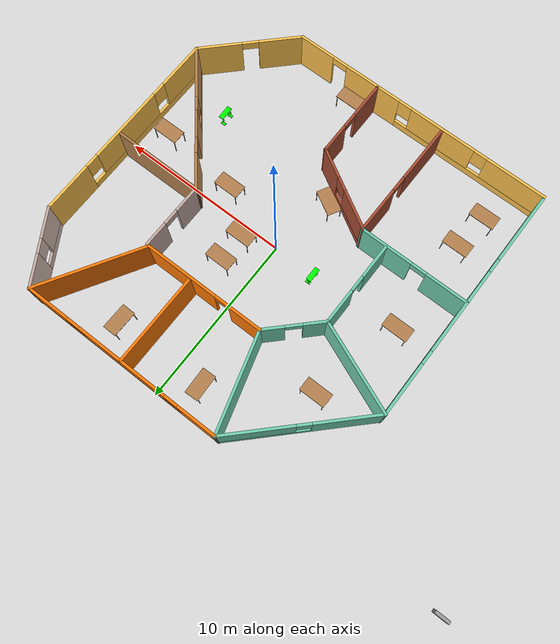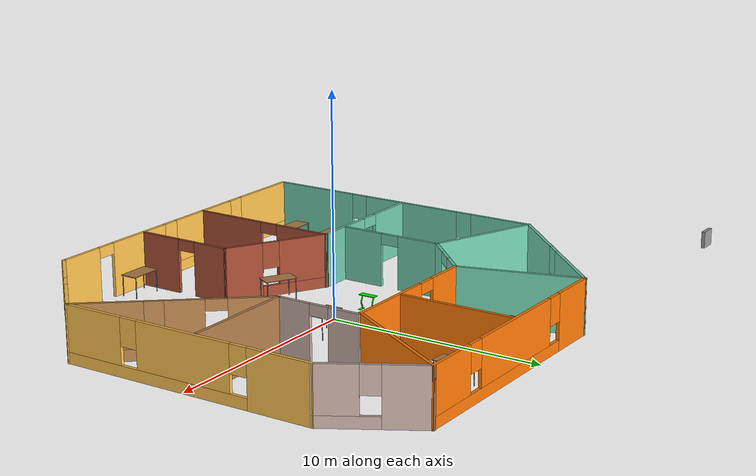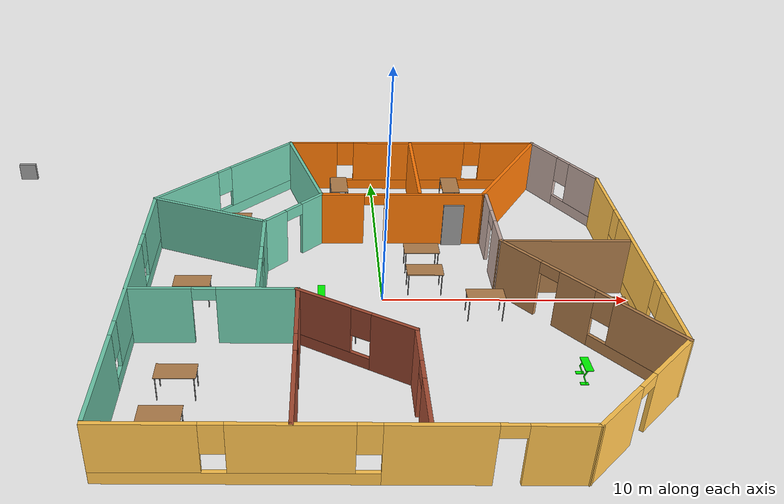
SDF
<sdf version="1.6">
 <world name="__default__">
  <plugin name="welcome_message" filename="libwelcome_message.so"/>
  <gravity>0 0 -9.8</gravity>
  <magnetic_field>6e-06 2.3e-05 -4.2e-05</magnetic_field>
  <atmosphere type="adiabatic"/>
  <physics type="ode">
   <max_step_size>0.001</max_step_size>
   <real_time_factor>1</real_time_factor>
   <real_time_update_rate>1000</real_time_update_rate>
  </physics>
  <scene><ambient>0.4 0.4 0.4 1</ambient><background>0.7 0.7 0.7 1</background><shadows>1</shadows></scene>
  <spherical_coordinates>
   <surface_model>EARTH_WGS84</surface_model>
   <latitude_deg>0</latitude_deg>
   <longitude_deg>0</longitude_deg>
   <elevation>0</elevation>
   <heading_deg>0</heading_deg>
  </spherical_coordinates>
  <model name="building">
   <pose>0.12432 -0.07335 0 0 -0 0</pose>
   <link name="Door_6">
    <collision name="Door_6_Collision">
     <geometry><box><size>0.9 0.17 2</size></box></geometry>
     <pose>0 0 1 0 -0 0</pose>
    </collision>
    <visual name="Door_6_Visual">
     <pose>0 0 1 0 -0 0</pose>
     <geometry><box><size>0.9 0.17 2</size></box></geometry>
     <material>
      <script><uri>file://media/materials/scripts/gazebo.material</uri><name>Gazebo/Grey</name></script>
     </material>
    </visual>
    <pose>3.22476 4.4878 0 0 -0 0</pose>
   </link>
   <link name="Wall_0">
    <pose>-9.87628 -2.77567 0 0 -0 1.5708</pose>
    <visual name="Wall_0_Visual_0">
     <pose>-4.91178 0 1.25 0 -0 0</pose>
     <geometry><box><size>4.17643 0.15 2.5</size></box></geometry>
     <material>
      <script><uri>file://media/materials/scripts/gazebo.material</uri><name>Gazebo/Grey</name></script>
      <ambient>0.435294 0.796078 0.67451 1</ambient>
     </material>
     <meta><layer>0</layer></meta>
    </visual>
    <collision name="Wall_0_Collision_0">
     <geometry><box><size>4.17643 0.15 2.5</size></box></geometry>
     <pose>-4.91178 0 1.25 0 -0 0</pose>
    </collision>
    <visual name="Wall_0_Visual_1">
     <pose>2.08822 0 0.25 0 -0 0</pose>
     <geometry><box><size>9.82357 0.15 0.5</size></box></geometry>
     <material>
      <script><uri>file://media/materials/scripts/gazebo.material</uri><name>Gazebo/Grey</name></script>
      <ambient>0.435294 0.796078 0.67451 1</ambient>
     </material>
     <meta><layer>0</layer></meta>
    </visual>
    <collision name="Wall_0_Collision_1">
     <geometry><box><size>9.82357 0.15 0.5</size></box></geometry>
     <pose>2.08822 0 0.25 0 -0 0</pose>
    </collision>
    <visual name="Wall_0_Visual_2">
     <pose>0.530704 0 1.5 0 -0 0</pose>
     <geometry><box><size>5.10854 0.15 2</size></box></geometry>
     <material>
      <script><uri>file://media/materials/scripts/gazebo.material</uri><name>Gazebo/Grey</name></script>
      <ambient>0.435294 0.796078 0.67451 1</ambient>
     </material>
     <meta><layer>0</layer></meta>
    </visual>
    <collision name="Wall_0_Collision_2">
     <geometry><box><size>5.10854 0.15 2</size></box></geometry>
     <pose>0.530704 0 1.5 0 -0 0</pose>
    </collision>
    <visual name="Wall_0_Visual_3">
     <pose>5.44249 0 1.5 0 -0 0</pose>
     <geometry><box><size>3.11503 0.15 2</size></box></geometry>
     <material>
      <script><uri>file://media/materials/scripts/gazebo.material</uri><name>Gazebo/Grey</name></script>
      <ambient>0.435294 0.796078 0.67451 1</ambient>
     </material>
     <meta><layer>0</layer></meta>
    </visual>
    <collision name="Wall_0_Collision_3">
     <geometry><box><size>3.11503 0.15 2</size></box></geometry>
     <pose>5.44249 0 1.5 0 -0 0</pose>
    </collision>
    <visual name="Wall_0_Visual_4">
     <pose>-2.42356 0 1.9 0 -0 0</pose>
     <geometry><box><size>0.8 0.15 1.2</size></box></geometry>
     <material>
      <script><uri>file://media/materials/scripts/gazebo.material</uri><name>Gazebo/Grey</name></script>
      <ambient>0.435294 0.796078 0.67451 1</ambient>
     </material>
     <meta><layer>0</layer></meta>
    </visual>
    <collision name="Wall_0_Collision_4">
     <geometry><box><size>0.8 0.15 1.2</size></box></geometry>
     <pose>-2.42356 0 1.9 0 -0 0</pose>
    </collision>
    <visual name="Wall_0_Visual_5">
     <pose>3.48497 0 1.9 0 -0 0</pose>
     <geometry><box><size>0.8 0.15 1.2</size></box></geometry>
     <material>
      <script><uri>file://media/materials/scripts/gazebo.material</uri><name>Gazebo/Grey</name></script>
      <ambient>0.435294 0.796078 0.67451 1</ambient>
     </material>
     <meta><layer>0</layer></meta>
    </visual>
    <collision name="Wall_0_Collision_5">
     <geometry><box><size>0.8 0.15 1.2</size></box></geometry>
     <pose>3.48497 0 1.9 0 -0 0</pose>
    </collision>
   </link>
   <link name="Wall_10">
    <pose>-6.6982 -2.75163 0 0 -0 3.14159</pose>
    <visual name="Wall_10_Visual_0">
     <pose>-1.70542 0 1.25 0 -0 0</pose>
     <geometry><box><size>3.08916 0.15 2.5</size></box></geometry>
     <material>
      <script><uri>file://media/materials/scripts/gazebo.material</uri><name>Gazebo/Grey</name></script>
      <ambient>0.435294 0.796078 0.67451 1</ambient>
     </material>
     <meta><layer>0</layer></meta>
    </visual>
    <collision name="Wall_10_Collision_0">
     <geometry><box><size>3.08916 0.15 2.5</size></box></geometry>
     <pose>-1.70542 0 1.25 0 -0 0</pose>
    </collision>
    <visual name="Wall_10_Visual_1">
     <pose>1.99458 0 1.25 0 -0 0</pose>
     <geometry><box><size>2.51084 0.15 2.5</size></box></geometry>
     <material>
      <script><uri>file://media/materials/scripts/gazebo.material</uri><name>Gazebo/Grey</name></script>
      <ambient>0.435294 0.796078 0.67451 1</ambient>
     </material>
     <meta><layer>0</layer></meta>
    </visual>
    <collision name="Wall_10_Collision_1">
     <geometry><box><size>2.51084 0.15 2.5</size></box></geometry>
     <pose>1.99458 0 1.25 0 -0 0</pose>
    </collision>
    <visual name="Wall_10_Visual_2">
     <pose>0.289158 0 2.25 0 -0 0</pose>
     <geometry><box><size>0.9 0.15 0.5</size></box></geometry>
     <material>
      <script><uri>file://media/materials/scripts/gazebo.material</uri><name>Gazebo/Grey</name></script>
      <ambient>0.435294 0.796078 0.67451 1</ambient>
     </material>
     <meta><layer>0</layer></meta>
    </visual>
    <collision name="Wall_10_Collision_2">
     <geometry><box><size>0.9 0.15 0.5</size></box></geometry>
     <pose>0.289158 0 2.25 0 -0 0</pose>
    </collision>
   </link>
   <link name="Wall_12">
    <pose>-5.00707 -0.228489 0 0 -0 1.5708</pose>
    <visual name="Wall_12_Visual_0">
     <pose>-1.49142 0 1.25 0 -0 0</pose>
     <geometry><box><size>2.01716 0.15 2.5</size></box></geometry>
     <material>
      <script><uri>file://media/materials/scripts/gazebo.material</uri><name>Gazebo/Grey</name></script>
      <ambient>0.435294 0.796078 0.67451 1</ambient>
     </material>
     <meta><layer>0</layer></meta>
    </visual>
    <collision name="Wall_12_Collision_0">
     <geometry><box><size>2.01716 0.15 2.5</size></box></geometry>
     <pose>-1.49142 0 1.25 0 -0 0</pose>
    </collision>
    <visual name="Wall_12_Visual_1">
     <pose>1.45858 0 1.25 0 -0 0</pose>
     <geometry><box><size>2.08284 0.15 2.5</size></box></geometry>
     <material>
      <script><uri>file://media/materials/scripts/gazebo.material</uri><name>Gazebo/Grey</name></script>
      <ambient>0.435294 0.796078 0.67451 1</ambient>
     </material>
     <meta><layer>0</layer></meta>
    </visual>
    <collision name="Wall_12_Collision_1">
     <geometry><box><size>2.08284 0.15 2.5</size></box></geometry>
     <pose>1.45858 0 1.25 0 -0 0</pose>
    </collision>
    <visual name="Wall_12_Visual_2">
     <pose>-0.032844 0 2.25 0 -0 0</pose>
     <geometry><box><size>0.9 0.15 0.5</size></box></geometry>
     <material>
      <script><uri>file://media/materials/scripts/gazebo.material</uri><name>Gazebo/Grey</name></script>
      <ambient>0.435294 0.796078 0.67451 1</ambient>
     </material>
     <meta><layer>0</layer></meta>
    </visual>
    <collision name="Wall_12_Collision_2">
     <geometry><box><size>0.9 0.15 0.5</size></box></geometry>
     <pose>-0.032844 0 2.25 0 -0 0</pose>
    </collision>
   </link>
   <link name="Wall_13">
    <collision name="Wall_13_Collision">
     <geometry><box><size>5.39621 0.15 2.5</size></box></geometry>
     <pose>0 0 1.25 0 -0 0</pose>
    </collision>
    <visual name="Wall_13_Visual">
     <pose>0 0 1.25 0 -0 0</pose>
     <geometry><box><size>5.39621 0.15 2.5</size></box></geometry>
     <material>
      <script><uri>file://media/materials/scripts/gazebo.material</uri><name>Gazebo/Grey</name></script>
      <ambient>0.435294 0.796078 0.67451 1</ambient>
     </material>
     <meta><layer>0</layer></meta>
    </visual>
    <pose>-7.44168 3.17292 0 0 -0 2.76018</pose>
   </link>
   <link name="Wall_15">
    <pose>-3.82267 3.38091 0 0 -0 0.785398</pose>
    <visual name="Wall_15_Visual_0">
     <pose>-1.10253 0 1.25 0 -0 0</pose>
     <geometry><box><size>1.29494 0.15 2.5</size></box></geometry>
     <material>
      <script><uri>file://media/materials/scripts/gazebo.material</uri><name>Gazebo/Grey</name></script>
      <ambient>0.435294 0.796078 0.67451 1</ambient>
     </material>
     <meta><layer>0</layer></meta>
    </visual>
    <collision name="Wall_15_Collision_0">
     <geometry><box><size>1.29494 0.15 2.5</size></box></geometry>
     <pose>-1.10253 0 1.25 0 -0 0</pose>
    </collision>
    <visual name="Wall_15_Visual_1">
     <pose>1.09747 0 1.25 0 -0 0</pose>
     <geometry><box><size>1.30506 0.15 2.5</size></box></geometry>
     <material>
      <script><uri>file://media/materials/scripts/gazebo.material</uri><name>Gazebo/Grey</name></script>
      <ambient>0.435294 0.796078 0.67451 1</ambient>
     </material>
     <meta><layer>0</layer></meta>
    </visual>
    <collision name="Wall_15_Collision_1">
     <geometry><box><size>1.30506 0.15 2.5</size></box></geometry>
     <pose>1.09747 0 1.25 0 -0 0</pose>
    </collision>
    <visual name="Wall_15_Visual_2">
     <pose>-0.005064 0 2.25 0 -0 0</pose>
     <geometry><box><size>0.9 0.15 0.5</size></box></geometry>
     <material>
      <script><uri>file://media/materials/scripts/gazebo.material</uri><name>Gazebo/Grey</name></script>
      <ambient>0.435294 0.796078 0.67451 1</ambient>
     </material>
     <meta><layer>0</layer></meta>
    </visual>
    <collision name="Wall_15_Collision_2">
     <geometry><box><size>0.9 0.15 0.5</size></box></geometry>
     <pose>-0.005064 0 2.25 0 -0 0</pose>
    </collision>
   </link>
   <link name="Wall_16">
    <pose>0.911739 4.56532 0 0 -0 0</pose>
    <visual name="Wall_16_Visual_0">
     <pose>-2.63993 0 1.25 0 -0 0</pose>
     <geometry><box><size>1.97015 0.15 2.5</size></box></geometry>
     <material>
      <script><uri>file://media/materials/scripts/gazebo.material</uri><name>Gazebo/Grey</name></script>
      <ambient>0.996078 0.47451 0.0196078 1</ambient>
     </material>
     <meta><layer>0</layer></meta>
    </visual>
    <collision name="Wall_16_Collision_0">
     <geometry><box><size>1.97015 0.15 2.5</size></box></geometry>
     <pose>-2.63993 0 1.25 0 -0 0</pose>
    </collision>
    <visual name="Wall_16_Visual_1">
     <pose>1.43507 0 1.25 0 -0 0</pose>
     <geometry><box><size>4.37985 0.15 2.5</size></box></geometry>
     <material>
      <script><uri>file://media/materials/scripts/gazebo.material</uri><name>Gazebo/Grey</name></script>
      <ambient>0.996078 0.47451 0.0196078 1</ambient>
     </material>
     <meta><layer>0</layer></meta>
    </visual>
    <collision name="Wall_16_Collision_1">
     <geometry><box><size>4.37985 0.15 2.5</size></box></geometry>
     <pose>1.43507 0 1.25 0 -0 0</pose>
    </collision>
    <visual name="Wall_16_Visual_2">
     <pose>-1.20485 0 2.25 0 -0 0</pose>
     <geometry><box><size>0.9 0.15 0.5</size></box></geometry>
     <material>
      <script><uri>file://media/materials/scripts/gazebo.material</uri><name>Gazebo/Grey</name></script>
      <ambient>0.996078 0.47451 0.0196078 1</ambient>
     </material>
     <meta><layer>0</layer></meta>
    </visual>
    <collision name="Wall_16_Collision_2">
     <geometry><box><size>0.9 0.15 0.5</size></box></geometry>
     <pose>-1.20485 0 2.25 0 -0 0</pose>
    </collision>
   </link>
   <link name="Wall_17">
    <collision name="Wall_17_Collision">
     <geometry><box><size>6.37153 0.15 2.5</size></box></geometry>
     <pose>0 0 1.25 0 -0 0</pose>
    </collision>
    <visual name="Wall_17_Visual">
     <pose>0 0 1.25 0 -0 0</pose>
     <geometry><box><size>6.37153 0.15 2.5</size></box></geometry>
     <material>
      <script><uri>file://media/materials/scripts/gazebo.material</uri><name>Gazebo/Grey</name></script>
      <ambient>0.996078 0.47451 0.0196078 1</ambient>
     </material>
     <meta><layer>0</layer></meta>
    </visual>
    <pose>6.08151 7.22111 0 0 -0 1.02313</pose>
   </link>
   <link name="Wall_19">
    <collision name="Wall_19_Collision">
     <geometry><box><size>5.67216 0.15 2.5</size></box></geometry>
     <pose>0 0 1.25 0 -0 0</pose>
    </collision>
    <visual name="Wall_19_Visual">
     <pose>0 0 1.25 0 -0 0</pose>
     <geometry><box><size>5.67216 0.15 2.5</size></box></geometry>
     <material>
      <script><uri>file://media/materials/scripts/gazebo.material</uri><name>Gazebo/Grey</name></script>
      <ambient>0.435294 0.796078 0.67451 1</ambient>
     </material>
     <meta><layer>0</layer></meta>
    </visual>
    <pose>-3.39349 7.22111 0 0 -0 1.84785</pose>
   </link>
   <link name="Wall_2">
    <pose>-7.0125 7.01311 0 0 -0 0.785398</pose>
    <visual name="Wall_2_Visual_0">
     <pose>-2.34585 0 1.25 0 -0 0</pose>
     <geometry><box><size>3.55829 0.15 2.5</size></box></geometry>
     <material>
      <script><uri>file://media/materials/scripts/gazebo.material</uri><name>Gazebo/Grey</name></script>
      <ambient>0.435294 0.796078 0.67451 1</ambient>
     </material>
     <meta><layer>0</layer></meta>
    </visual>
    <collision name="Wall_2_Collision_0">
     <geometry><box><size>3.55829 0.15 2.5</size></box></geometry>
     <pose>-2.34585 0 1.25 0 -0 0</pose>
    </collision>
    <visual name="Wall_2_Visual_1">
     <pose>1.77914 0 0.25 0 -0 0</pose>
     <geometry><box><size>4.69171 0.15 0.5</size></box></geometry>
     <material>
      <script><uri>file://media/materials/scripts/gazebo.material</uri><name>Gazebo/Grey</name></script>
      <ambient>0.435294 0.796078 0.67451 1</ambient>
     </material>
     <meta><layer>0</layer></meta>
    </visual>
    <collision name="Wall_2_Collision_1">
     <geometry><box><size>4.69171 0.15 0.5</size></box></geometry>
     <pose>1.77914 0 0.25 0 -0 0</pose>
    </collision>
    <visual name="Wall_2_Visual_2">
     <pose>2.1627 0 1.5 0 -0 0</pose>
     <geometry><box><size>3.92461 0.15 2</size></box></geometry>
     <material>
      <script><uri>file://media/materials/scripts/gazebo.material</uri><name>Gazebo/Grey</name></script>
      <ambient>0.435294 0.796078 0.67451 1</ambient>
     </material>
     <meta><layer>0</layer></meta>
    </visual>
    <collision name="Wall_2_Collision_2">
     <geometry><box><size>3.92461 0.15 2</size></box></geometry>
     <pose>2.1627 0 1.5 0 -0 0</pose>
    </collision>
    <visual name="Wall_2_Visual_3">
     <pose>-0.183159 0 1.9 0 -0 0</pose>
     <geometry><box><size>0.767103 0.15 1.2</size></box></geometry>
     <material>
      <script><uri>file://media/materials/scripts/gazebo.material</uri><name>Gazebo/Grey</name></script>
      <ambient>0.435294 0.796078 0.67451 1</ambient>
     </material>
     <meta><layer>0</layer></meta>
    </visual>
    <collision name="Wall_2_Collision_3">
     <geometry><box><size>0.767103 0.15 1.2</size></box></geometry>
     <pose>-0.183159 0 1.9 0 -0 0</pose>
    </collision>
   </link>
   <link name="Wall_21">
    <collision name="Wall_21_Collision">
     <geometry><box><size>5.25 0.15 2.5</size></box></geometry>
     <pose>0 0 1.25 0 -0 0</pose>
    </collision>
    <visual name="Wall_21_Visual">
     <pose>0 0 1.25 0 -0 0</pose>
     <geometry><box><size>5.25 0.15 2.5</size></box></geometry>
     <material>
      <script><uri>file://media/materials/scripts/gazebo.material</uri><name>Gazebo/Grey</name></script>
      <ambient>0.996078 0.47451 0.0196078 1</ambient>
     </material>
     <meta><layer>0</layer></meta>
    </visual>
    <pose>1.71208 7.28497 0 0 0 -1.5708</pose>
   </link>
   <link name="Wall_23">
    <pose>0.656712 -7.49478 0 0 -0 1.5708</pose>
    <visual name="Wall_23_Visual_0">
     <pose>-1.33124 0 1.25 0 -0 0</pose>
     <geometry><box><size>2.08751 0.15 2.5</size></box></geometry>
     <material>
      <script><uri>file://media/materials/scripts/gazebo.material</uri><name>Gazebo/Bricks</name></script>
      <ambient>1 1 1 1</ambient>
     </material>
     <meta><layer>0</layer></meta>
    </visual>
    <collision name="Wall_23_Collision_0">
     <geometry><box><size>2.08751 0.15 2.5</size></box></geometry>
     <pose>-1.33124 0 1.25 0 -0 0</pose>
    </collision>
    <visual name="Wall_23_Visual_1">
     <pose>1.49376 0 1.25 0 -0 0</pose>
     <geometry><box><size>1.76249 0.15 2.5</size></box></geometry>
     <material>
      <script><uri>file://media/materials/scripts/gazebo.material</uri><name>Gazebo/Bricks</name></script>
      <ambient>1 1 1 1</ambient>
     </material>
     <meta><layer>0</layer></meta>
    </visual>
    <collision name="Wall_23_Collision_1">
     <geometry><box><size>1.76249 0.15 2.5</size></box></geometry>
     <pose>1.49376 0 1.25 0 -0 0</pose>
    </collision>
    <visual name="Wall_23_Visual_2">
     <pose>0.162514 0 2.25 0 -0 0</pose>
     <geometry><box><size>0.9 0.15 0.5</size></box></geometry>
     <material>
      <script><uri>file://media/materials/scripts/gazebo.material</uri><name>Gazebo/Bricks</name></script>
      <ambient>1 1 1 1</ambient>
     </material>
     <meta><layer>0</layer></meta>
    </visual>
    <collision name="Wall_23_Collision_2">
     <geometry><box><size>0.9 0.15 0.5</size></box></geometry>
     <pose>0.162514 0 2.25 0 -0 0</pose>
    </collision>
   </link>
   <link name="Wall_24">
    <pose>-1.4434 -3.98228 0 0 -0 2.61799</pose>
    <visual name="Wall_24_Visual_0">
     <pose>-1.59157 0 1.25 0 -0 0</pose>
     <geometry><box><size>1.81686 0.15 2.5</size></box></geometry>
     <material>
      <script><uri>file://media/materials/scripts/gazebo.material</uri><name>Gazebo/Bricks</name></script>
      <ambient>1 1 1 1</ambient>
     </material>
     <meta><layer>0</layer></meta>
    </visual>
    <collision name="Wall_24_Collision_0">
     <geometry><box><size>1.81686 0.15 2.5</size></box></geometry>
     <pose>-1.59157 0 1.25 0 -0 0</pose>
    </collision>
    <visual name="Wall_24_Visual_1">
     <pose>0.90843 0 0.25 0 -0 0</pose>
     <geometry><box><size>3.18314 0.15 0.5</size></box></geometry>
     <material>
      <script><uri>file://media/materials/scripts/gazebo.material</uri><name>Gazebo/Bricks</name></script>
      <ambient>1 1 1 1</ambient>
     </material>
     <meta><layer>0</layer></meta>
    </visual>
    <collision name="Wall_24_Collision_1">
     <geometry><box><size>3.18314 0.15 0.5</size></box></geometry>
     <pose>0.90843 0 0.25 0 -0 0</pose>
    </collision>
    <visual name="Wall_24_Visual_2">
     <pose>1.30843 0 1.5 0 -0 0</pose>
     <geometry><box><size>2.38314 0.15 2</size></box></geometry>
     <material>
      <script><uri>file://media/materials/scripts/gazebo.material</uri><name>Gazebo/Bricks</name></script>
      <ambient>1 1 1 1</ambient>
     </material>
     <meta><layer>0</layer></meta>
    </visual>
    <collision name="Wall_24_Collision_2">
     <geometry><box><size>2.38314 0.15 2</size></box></geometry>
     <pose>1.30843 0 1.5 0 -0 0</pose>
    </collision>
    <visual name="Wall_24_Visual_3">
     <pose>-0.283141 0 1.9 0 -0 0</pose>
     <geometry><box><size>0.8 0.15 1.2</size></box></geometry>
     <material>
      <script><uri>file://media/materials/scripts/gazebo.material</uri><name>Gazebo/Bricks</name></script>
      <ambient>1 1 1 1</ambient>
     </material>
     <meta><layer>0</layer></meta>
    </visual>
    <collision name="Wall_24_Collision_3">
     <geometry><box><size>0.8 0.15 1.2</size></box></geometry>
     <pose>-0.283141 0 1.9 0 -0 0</pose>
    </collision>
   </link>
   <link name="Wall_26">
    <collision name="Wall_26_Collision">
     <geometry><box><size>5.25 0.15 2.5</size></box></geometry>
     <pose>0 0 1.25 0 -0 0</pose>
    </collision>
    <visual name="Wall_26_Visual">
     <pose>0 0 1.25 0 -0 0</pose>
     <geometry><box><size>5.25 0.15 2.5</size></box></geometry>
     <material>
      <script><uri>file://media/materials/scripts/gazebo.material</uri><name>Gazebo/Wood</name></script>
      <ambient>0.760784 0.662745 0.627451 1</ambient>
     </material>
     <meta><layer>0</layer></meta>
    </visual>
    <pose>7.14765 0.688493 0 0 -0 3.14159</pose>
   </link>
   <link name="Wall_27">
    <pose>4.59765 2.61349 0 0 -0 1.5708</pose>
    <visual name="Wall_27_Visual_0">
     <pose>-1.18491 0 1.25 0 -0 0</pose>
     <geometry><box><size>1.63019 0.15 2.5</size></box></geometry>
     <material>
      <script><uri>file://media/materials/scripts/gazebo.material</uri><name>Gazebo/Grey</name></script>
      <ambient>0.760784 0.662745 0.627451 1</ambient>
     </material>
     <meta><layer>0</layer></meta>
    </visual>
    <collision name="Wall_27_Collision_0">
     <geometry><box><size>1.63019 0.15 2.5</size></box></geometry>
     <pose>-1.18491 0 1.25 0 -0 0</pose>
    </collision>
    <visual name="Wall_27_Visual_1">
     <pose>1.2651 0 1.25 0 -0 0</pose>
     <geometry><box><size>1.46981 0.15 2.5</size></box></geometry>
     <material>
      <script><uri>file://media/materials/scripts/gazebo.material</uri><name>Gazebo/Grey</name></script>
      <ambient>0.760784 0.662745 0.627451 1</ambient>
     </material>
     <meta><layer>0</layer></meta>
    </visual>
    <collision name="Wall_27_Collision_1">
     <geometry><box><size>1.46981 0.15 2.5</size></box></geometry>
     <pose>1.2651 0 1.25 0 -0 0</pose>
    </collision>
    <visual name="Wall_27_Visual_2">
     <pose>0.080189 0 2.25 0 -0 0</pose>
     <geometry><box><size>0.9 0.15 0.5</size></box></geometry>
     <material>
      <script><uri>file://media/materials/scripts/gazebo.material</uri><name>Gazebo/Grey</name></script>
      <ambient>0.760784 0.662745 0.627451 1</ambient>
     </material>
     <meta><layer>0</layer></meta>
    </visual>
    <collision name="Wall_27_Collision_2">
     <geometry><box><size>0.9 0.15 0.5</size></box></geometry>
     <pose>0.080189 0 2.25 0 -0 0</pose>
    </collision>
   </link>
   <link name="Wall_29">
    <pose>7.23697 -2.52591 0 0 0 -0.883328</pose>
    <visual name="Wall_29_Visual_0">
     <pose>-3.18456 0 1.25 0 -0 0</pose>
     <geometry><box><size>2.09914 0.15 2.5</size></box></geometry>
     <material>
      <script><uri>file://media/materials/scripts/gazebo.material</uri><name>Gazebo/Wood</name></script>
      <ambient>0.760784 0.662745 0.627451 1</ambient>
     </material>
     <meta><layer>0</layer></meta>
    </visual>
    <collision name="Wall_29_Collision_0">
     <geometry><box><size>2.09914 0.15 2.5</size></box></geometry>
     <pose>-3.18456 0 1.25 0 -0 0</pose>
    </collision>
    <visual name="Wall_29_Visual_1">
     <pose>-0.426058 0 1.25 0 -0 0</pose>
     <geometry><box><size>1.61787 0.15 2.5</size></box></geometry>
     <material>
      <script><uri>file://media/materials/scripts/gazebo.material</uri><name>Gazebo/Wood</name></script>
      <ambient>0.760784 0.662745 0.627451 1</ambient>
     </material>
     <meta><layer>0</layer></meta>
    </visual>
    <collision name="Wall_29_Collision_1">
     <geometry><box><size>1.61787 0.15 2.5</size></box></geometry>
     <pose>-0.426058 0 1.25 0 -0 0</pose>
    </collision>
    <visual name="Wall_29_Visual_2">
     <pose>2.3085 0 0.25 0 -0 0</pose>
     <geometry><box><size>3.85126 0.15 0.5</size></box></geometry>
     <material>
      <script><uri>file://media/materials/scripts/gazebo.material</uri><name>Gazebo/Wood</name></script>
      <ambient>0.760784 0.662745 0.627451 1</ambient>
     </material>
     <meta><layer>0</layer></meta>
    </visual>
    <collision name="Wall_29_Collision_2">
     <geometry><box><size>3.85126 0.15 0.5</size></box></geometry>
     <pose>2.3085 0 0.25 0 -0 0</pose>
    </collision>
    <visual name="Wall_29_Visual_3">
     <pose>2.7085 0 1.5 0 -0 0</pose>
     <geometry><box><size>3.05126 0.15 2</size></box></geometry>
     <material>
      <script><uri>file://media/materials/scripts/gazebo.material</uri><name>Gazebo/Wood</name></script>
      <ambient>0.760784 0.662745 0.627451 1</ambient>
     </material>
     <meta><layer>0</layer></meta>
    </visual>
    <collision name="Wall_29_Collision_3">
     <geometry><box><size>3.05126 0.15 2</size></box></geometry>
     <pose>2.7085 0 1.5 0 -0 0</pose>
    </collision>
    <visual name="Wall_29_Visual_4">
     <pose>0.782874 0 1.9 0 -0 0</pose>
     <geometry><box><size>0.8 0.15 1.2</size></box></geometry>
     <material>
      <script><uri>file://media/materials/scripts/gazebo.material</uri><name>Gazebo/Wood</name></script>
      <ambient>0.760784 0.662745 0.627451 1</ambient>
     </material>
     <meta><layer>0</layer></meta>
    </visual>
    <collision name="Wall_29_Collision_4">
     <geometry><box><size>0.8 0.15 1.2</size></box></geometry>
     <pose>0.782874 0 1.9 0 -0 0</pose>
    </collision>
    <visual name="Wall_29_Visual_5">
     <pose>-1.68499 0 2.25 0 -0 0</pose>
     <geometry><box><size>0.9 0.15 0.5</size></box></geometry>
     <material>
      <script><uri>file://media/materials/scripts/gazebo.material</uri><name>Gazebo/Wood</name></script>
      <ambient>0.760784 0.662745 0.627451 1</ambient>
     </material>
     <meta><layer>0</layer></meta>
    </visual>
    <collision name="Wall_29_Collision_5">
     <geometry><box><size>0.9 0.15 0.5</size></box></geometry>
     <pose>-1.68499 0 2.25 0 -0 0</pose>
    </collision>
   </link>
   <link name="Wall_3">
    <pose>1.77628 9.87689 0 0 -0 0</pose>
    <visual name="Wall_3_Visual_0">
     <pose>-4.81625 0 1.25 0 -0 0</pose>
     <geometry><box><size>2.3675 0.15 2.5</size></box></geometry>
     <material>
      <script><uri>file://media/materials/scripts/gazebo.material</uri><name>Gazebo/Grey</name></script>
      <ambient>0.996078 0.47451 0.0196078 1</ambient>
     </material>
     <meta><layer>0</layer></meta>
    </visual>
    <collision name="Wall_3_Collision_0">
     <geometry><box><size>2.3675 0.15 2.5</size></box></geometry>
     <pose>-4.81625 0 1.25 0 -0 0</pose>
    </collision>
    <visual name="Wall_3_Visual_1">
     <pose>1.18375 0 0.25 0 -0 0</pose>
     <geometry><box><size>9.6325 0.15 0.5</size></box></geometry>
     <material>
      <script><uri>file://media/materials/scripts/gazebo.material</uri><name>Gazebo/Grey</name></script>
      <ambient>0.996078 0.47451 0.0196078 1</ambient>
     </material>
     <meta><layer>0</layer></meta>
    </visual>
    <collision name="Wall_3_Collision_1">
     <geometry><box><size>9.6325 0.15 0.5</size></box></geometry>
     <pose>1.18375 0 0.25 0 -0 0</pose>
    </collision>
    <visual name="Wall_3_Visual_2">
     <pose>-0.115398 0 1.5 0 -0 0</pose>
     <geometry><box><size>5.43421 0.15 2</size></box></geometry>
     <material>
      <script><uri>file://media/materials/scripts/gazebo.material</uri><name>Gazebo/Grey</name></script>
      <ambient>0.996078 0.47451 0.0196078 1</ambient>
     </material>
     <meta><layer>0</layer></meta>
    </visual>
    <collision name="Wall_3_Collision_2">
     <geometry><box><size>5.43421 0.15 2</size></box></geometry>
     <pose>-0.115398 0 1.5 0 -0 0</pose>
    </collision>
    <visual name="Wall_3_Visual_3">
     <pose>4.70085 0 1.5 0 -0 0</pose>
     <geometry><box><size>2.5983 0.15 2</size></box></geometry>
     <material>
      <script><uri>file://media/materials/scripts/gazebo.material</uri><name>Gazebo/Grey</name></script>
      <ambient>0.996078 0.47451 0.0196078 1</ambient>
     </material>
     <meta><layer>0</layer></meta>
    </visual>
    <collision name="Wall_3_Collision_3">
     <geometry><box><size>2.5983 0.15 2</size></box></geometry>
     <pose>4.70085 0 1.5 0 -0 0</pose>
    </collision>
    <visual name="Wall_3_Visual_4">
     <pose>-3.2325 0 1.9 0 -0 0</pose>
     <geometry><box><size>0.8 0.15 1.2</size></box></geometry>
     <material>
      <script><uri>file://media/materials/scripts/gazebo.material</uri><name>Gazebo/Grey</name></script>
      <ambient>0.996078 0.47451 0.0196078 1</ambient>
     </material>
     <meta><layer>0</layer></meta>
    </visual>
    <collision name="Wall_3_Collision_4">
     <geometry><box><size>0.8 0.15 1.2</size></box></geometry>
     <pose>-3.2325 0 1.9 0 -0 0</pose>
    </collision>
    <visual name="Wall_3_Visual_5">
     <pose>3.0017 0 1.9 0 -0 0</pose>
     <geometry><box><size>0.8 0.15 1.2</size></box></geometry>
     <material>
      <script><uri>file://media/materials/scripts/gazebo.material</uri><name>Gazebo/Grey</name></script>
      <ambient>0.996078 0.47451 0.0196078 1</ambient>
     </material>
     <meta><layer>0</layer></meta>
    </visual>
    <collision name="Wall_3_Collision_5">
     <geometry><box><size>0.8 0.15 1.2</size></box></geometry>
     <pose>3.0017 0 1.9 0 -0 0</pose>
    </collision>
   </link>
   <link name="Wall_4">
    <pose>8.78878 7.99329 0 0 0 -1.0472</pose>
    <visual name="Wall_4_Visual_0">
     <pose>-1.2928 0 1.25 0 -0 0</pose>
     <geometry><box><size>1.91439 0.15 2.5</size></box></geometry>
     <material>
      <script><uri>file://media/materials/scripts/gazebo.material</uri><name>Gazebo/Grey</name></script>
      <ambient>0.760784 0.662745 0.627451 1</ambient>
     </material>
     <meta><layer>0</layer></meta>
    </visual>
    <collision name="Wall_4_Collision_0">
     <geometry><box><size>1.91439 0.15 2.5</size></box></geometry>
     <pose>-1.2928 0 1.25 0 -0 0</pose>
    </collision>
    <visual name="Wall_4_Visual_1">
     <pose>0.957197 0 0.25 0 -0 0</pose>
     <geometry><box><size>2.58561 0.15 0.5</size></box></geometry>
     <material>
      <script><uri>file://media/materials/scripts/gazebo.material</uri><name>Gazebo/Grey</name></script>
      <ambient>0.760784 0.662745 0.627451 1</ambient>
     </material>
     <meta><layer>0</layer></meta>
    </visual>
    <collision name="Wall_4_Collision_1">
     <geometry><box><size>2.58561 0.15 0.5</size></box></geometry>
     <pose>0.957197 0 0.25 0 -0 0</pose>
    </collision>
    <visual name="Wall_4_Visual_2">
     <pose>1.3572 0 1.5 0 -0 0</pose>
     <geometry><box><size>1.78561 0.15 2</size></box></geometry>
     <material>
      <script><uri>file://media/materials/scripts/gazebo.material</uri><name>Gazebo/Grey</name></script>
      <ambient>0.760784 0.662745 0.627451 1</ambient>
     </material>
     <meta><layer>0</layer></meta>
    </visual>
    <collision name="Wall_4_Collision_2">
     <geometry><box><size>1.78561 0.15 2</size></box></geometry>
     <pose>1.3572 0 1.5 0 -0 0</pose>
    </collision>
    <visual name="Wall_4_Visual_3">
     <pose>0.064394 0 1.9 0 -0 0</pose>
     <geometry><box><size>0.8 0.15 1.2</size></box></geometry>
     <material>
      <script><uri>file://media/materials/scripts/gazebo.material</uri><name>Gazebo/Grey</name></script>
      <ambient>0.760784 0.662745 0.627451 1</ambient>
     </material>
     <meta><layer>0</layer></meta>
    </visual>
    <collision name="Wall_4_Collision_3">
     <geometry><box><size>0.8 0.15 1.2</size></box></geometry>
     <pose>0.064394 0 1.9 0 -0 0</pose>
    </collision>
   </link>
   <link name="Wall_5">
    <pose>9.87628 0.184682 0 0 0 -1.5708</pose>
    <visual name="Wall_5_Visual_0">
     <pose>-4.5091 0 1.25 0 -0 0</pose>
     <geometry><box><size>2.98181 0.15 2.5</size></box></geometry>
     <material>
      <script><uri>file://media/materials/scripts/gazebo.material</uri><name>Gazebo/Grey</name></script>
      <ambient>1 0.764706 0.305882 1</ambient>
     </material>
     <meta><layer>0</layer></meta>
    </visual>
    <collision name="Wall_5_Collision_0">
     <geometry><box><size>2.98181 0.15 2.5</size></box></geometry>
     <pose>-4.5091 0 1.25 0 -0 0</pose>
    </collision>
    <visual name="Wall_5_Visual_1">
     <pose>1.4909 0 0.25 0 -0 0</pose>
     <geometry><box><size>9.01819 0.15 0.5</size></box></geometry>
     <material>
      <script><uri>file://media/materials/scripts/gazebo.material</uri><name>Gazebo/Grey</name></script>
      <ambient>1 0.764706 0.305882 1</ambient>
     </material>
     <meta><layer>0</layer></meta>
    </visual>
    <collision name="Wall_5_Collision_1">
     <geometry><box><size>9.01819 0.15 0.5</size></box></geometry>
     <pose>1.4909 0 0.25 0 -0 0</pose>
    </collision>
    <visual name="Wall_5_Visual_2">
     <pose>0.056931 0 1.5 0 -0 0</pose>
     <geometry><box><size>4.55025 0.15 2</size></box></geometry>
     <material>
      <script><uri>file://media/materials/scripts/gazebo.material</uri><name>Gazebo/Grey</name></script>
      <ambient>1 0.764706 0.305882 1</ambient>
     </material>
     <meta><layer>0</layer></meta>
    </visual>
    <collision name="Wall_5_Collision_2">
     <geometry><box><size>4.55025 0.15 2</size></box></geometry>
     <pose>0.056931 0 1.5 0 -0 0</pose>
    </collision>
    <visual name="Wall_5_Visual_3">
     <pose>4.56603 0 1.5 0 -0 0</pose>
     <geometry><box><size>2.86794 0.15 2</size></box></geometry>
     <material>
      <script><uri>file://media/materials/scripts/gazebo.material</uri><name>Gazebo/Grey</name></script>
      <ambient>1 0.764706 0.305882 1</ambient>
     </material>
     <meta><layer>0</layer></meta>
    </visual>
    <collision name="Wall_5_Collision_3">
     <geometry><box><size>2.86794 0.15 2</size></box></geometry>
     <pose>4.56603 0 1.5 0 -0 0</pose>
    </collision>
    <visual name="Wall_5_Visual_4">
     <pose>-2.61819 0 1.9 0 -0 0</pose>
     <geometry><box><size>0.8 0.15 1.2</size></box></geometry>
     <material>
      <script><uri>file://media/materials/scripts/gazebo.material</uri><name>Gazebo/Grey</name></script>
      <ambient>1 0.764706 0.305882 1</ambient>
     </material>
     <meta><layer>0</layer></meta>
    </visual>
    <collision name="Wall_5_Collision_4">
     <geometry><box><size>0.8 0.15 1.2</size></box></geometry>
     <pose>-2.61819 0 1.9 0 -0 0</pose>
    </collision>
    <visual name="Wall_5_Visual_5">
     <pose>2.73206 0 1.9 0 -0 0</pose>
     <geometry><box><size>0.8 0.15 1.2</size></box></geometry>
     <material>
      <script><uri>file://media/materials/scripts/gazebo.material</uri><name>Gazebo/Grey</name></script>
      <ambient>1 0.764706 0.305882 1</ambient>
     </material>
     <meta><layer>0</layer></meta>
    </visual>
    <collision name="Wall_5_Collision_5">
     <geometry><box><size>0.8 0.15 1.2</size></box></geometry>
     <pose>2.73206 0 1.9 0 -0 0</pose>
    </collision>
   </link>
   <link name="Wall_6">
    <pose>7.80799 -7.80861 0 0 0 -2.35619</pose>
    <visual name="Wall_6_Visual_0">
     <pose>-1.70787 0 1.25 0 -0 0</pose>
     <geometry><box><size>2.58426 0.15 2.5</size></box></geometry>
     <material>
      <script><uri>file://media/materials/scripts/gazebo.material</uri><name>Gazebo/Grey</name></script>
      <ambient>1 0.764706 0.305882 1</ambient>
     </material>
     <meta><layer>0</layer></meta>
    </visual>
    <collision name="Wall_6_Collision_0">
     <geometry><box><size>2.58426 0.15 2.5</size></box></geometry>
     <pose>-1.70787 0 1.25 0 -0 0</pose>
    </collision>
    <visual name="Wall_6_Visual_1">
     <pose>1.74213 0 1.25 0 -0 0</pose>
     <geometry><box><size>2.51574 0.15 2.5</size></box></geometry>
     <material>
      <script><uri>file://media/materials/scripts/gazebo.material</uri><name>Gazebo/Grey</name></script>
      <ambient>1 0.764706 0.305882 1</ambient>
     </material>
     <meta><layer>0</layer></meta>
    </visual>
    <collision name="Wall_6_Collision_1">
     <geometry><box><size>2.51574 0.15 2.5</size></box></geometry>
     <pose>1.74213 0 1.25 0 -0 0</pose>
    </collision>
    <visual name="Wall_6_Visual_2">
     <pose>0.034258 0 2.25 0 -0 0</pose>
     <geometry><box><size>0.9 0.15 0.5</size></box></geometry>
     <material>
      <script><uri>file://media/materials/scripts/gazebo.material</uri><name>Gazebo/Grey</name></script>
      <ambient>1 0.764706 0.305882 1</ambient>
     </material>
     <meta><layer>0</layer></meta>
    </visual>
    <collision name="Wall_6_Collision_2">
     <geometry><box><size>0.9 0.15 0.5</size></box></geometry>
     <pose>0.034258 0 2.25 0 -0 0</pose>
    </collision>
   </link>
   <link name="Wall_7">
    <pose>-2.06029 -9.87689 0 0 -0 3.14159</pose>
    <visual name="Wall_7_Visual_0">
     <pose>-6.76985 0 1.25 0 -0 0</pose>
     <geometry><box><size>2.2103 0.15 2.5</size></box></geometry>
     <material>
      <script><uri>file://media/materials/scripts/gazebo.material</uri><name>Gazebo/Grey</name></script>
      <ambient>1 0.764706 0.305882 1</ambient>
     </material>
     <meta><layer>0</layer></meta>
    </visual>
    <collision name="Wall_7_Collision_0">
     <geometry><box><size>2.2103 0.15 2.5</size></box></geometry>
     <pose>-6.76985 0 1.25 0 -0 0</pose>
    </collision>
    <visual name="Wall_7_Visual_1">
     <pose>-3.02396 0 1.25 0 -0 0</pose>
     <geometry><box><size>3.48148 0.15 2.5</size></box></geometry>
     <material>
      <script><uri>file://media/materials/scripts/gazebo.material</uri><name>Gazebo/Grey</name></script>
      <ambient>1 0.764706 0.305882 1</ambient>
     </material>
     <meta><layer>0</layer></meta>
    </visual>
    <collision name="Wall_7_Collision_1">
     <geometry><box><size>3.48148 0.15 2.5</size></box></geometry>
     <pose>-3.02396 0 1.25 0 -0 0</pose>
    </collision>
    <visual name="Wall_7_Visual_2">
     <pose>3.29589 0 0.25 0 -0 0</pose>
     <geometry><box><size>9.15822 0.15 0.5</size></box></geometry>
     <material>
      <script><uri>file://media/materials/scripts/gazebo.material</uri><name>Gazebo/Grey</name></script>
      <ambient>1 0.764706 0.305882 1</ambient>
     </material>
     <meta><layer>0</layer></meta>
    </visual>
    <collision name="Wall_7_Collision_2">
     <geometry><box><size>9.15822 0.15 0.5</size></box></geometry>
     <pose>3.29589 0 0.25 0 -0 0</pose>
    </collision>
    <visual name="Wall_7_Visual_3">
     <pose>1.51276 0 1.5 0 -0 0</pose>
     <geometry><box><size>3.99196 0.15 2</size></box></geometry>
     <material>
      <script><uri>file://media/materials/scripts/gazebo.material</uri><name>Gazebo/Grey</name></script>
      <ambient>1 0.764706 0.305882 1</ambient>
     </material>
     <meta><layer>0</layer></meta>
    </visual>
    <collision name="Wall_7_Collision_3">
     <geometry><box><size>3.99196 0.15 2</size></box></geometry>
     <pose>1.51276 0 1.5 0 -0 0</pose>
    </collision>
    <visual name="Wall_7_Visual_4">
     <pose>6.09187 0 1.5 0 -0 0</pose>
     <geometry><box><size>3.56625 0.15 2</size></box></geometry>
     <material>
      <script><uri>file://media/materials/scripts/gazebo.material</uri><name>Gazebo/Grey</name></script>
      <ambient>1 0.764706 0.305882 1</ambient>
     </material>
     <meta><layer>0</layer></meta>
    </visual>
    <collision name="Wall_7_Collision_4">
     <geometry><box><size>3.56625 0.15 2</size></box></geometry>
     <pose>6.09187 0 1.5 0 -0 0</pose>
    </collision>
    <visual name="Wall_7_Visual_5">
     <pose>-0.883218 0 1.9 0 -0 0</pose>
     <geometry><box><size>0.8 0.15 1.2</size></box></geometry>
     <material>
      <script><uri>file://media/materials/scripts/gazebo.material</uri><name>Gazebo/Grey</name></script>
      <ambient>1 0.764706 0.305882 1</ambient>
     </material>
     <meta><layer>0</layer></meta>
    </visual>
    <collision name="Wall_7_Collision_5">
     <geometry><box><size>0.8 0.15 1.2</size></box></geometry>
     <pose>-0.883218 0 1.9 0 -0 0</pose>
    </collision>
    <visual name="Wall_7_Visual_6">
     <pose>3.90875 0 1.9 0 -0 0</pose>
     <geometry><box><size>0.8 0.15 1.2</size></box></geometry>
     <material>
      <script><uri>file://media/materials/scripts/gazebo.material</uri><name>Gazebo/Grey</name></script>
      <ambient>1 0.764706 0.305882 1</ambient>
     </material>
     <meta><layer>0</layer></meta>
    </visual>
    <collision name="Wall_7_Collision_6">
     <geometry><box><size>0.8 0.15 1.2</size></box></geometry>
     <pose>3.90875 0 1.9 0 -0 0</pose>
    </collision>
    <visual name="Wall_7_Visual_7">
     <pose>-5.2147 0 2.25 0 -0 0</pose>
     <geometry><box><size>0.9 0.15 0.5</size></box></geometry>
     <material>
      <script><uri>file://media/materials/scripts/gazebo.material</uri><name>Gazebo/Grey</name></script>
      <ambient>1 0.764706 0.305882 1</ambient>
     </material>
     <meta><layer>0</layer></meta>
    </visual>
    <collision name="Wall_7_Collision_7">
     <geometry><box><size>0.9 0.15 0.5</size></box></geometry>
     <pose>-5.2147 0 2.25 0 -0 0</pose>
    </collision>
   </link>
   <link name="Wall_9">
    <pose>-3.52319 -6.30163 0 0 -0 1.5633</pose>
    <visual name="Wall_9_Visual_0">
     <pose>-1.84607 0 1.25 0 -0 0</pose>
     <geometry><box><size>3.55786 0.15 2.5</size></box></geometry>
     <material>
      <script><uri>file://media/materials/scripts/gazebo.material</uri><name>Gazebo/Bricks</name></script>
      <ambient>1 1 1 1</ambient>
     </material>
     <meta><layer>0</layer></meta>
    </visual>
    <collision name="Wall_9_Collision_0">
     <geometry><box><size>3.55786 0.15 2.5</size></box></geometry>
     <pose>-1.84607 0 1.25 0 -0 0</pose>
    </collision>
    <visual name="Wall_9_Visual_1">
     <pose>2.22893 0 1.25 0 -0 0</pose>
     <geometry><box><size>2.79214 0.15 2.5</size></box></geometry>
     <material>
      <script><uri>file://media/materials/scripts/gazebo.material</uri><name>Gazebo/Bricks</name></script>
      <ambient>1 1 1 1</ambient>
     </material>
     <meta><layer>0</layer></meta>
    </visual>
    <collision name="Wall_9_Collision_1">
     <geometry><box><size>2.79214 0.15 2.5</size></box></geometry>
     <pose>2.22893 0 1.25 0 -0 0</pose>
    </collision>
    <visual name="Wall_9_Visual_2">
     <pose>0.382859 0 2.25 0 -0 0</pose>
     <geometry><box><size>0.9 0.15 0.5</size></box></geometry>
     <material>
      <script><uri>file://media/materials/scripts/gazebo.material</uri><name>Gazebo/Bricks</name></script>
      <ambient>1 1 1 1</ambient>
     </material>
     <meta><layer>0</layer></meta>
    </visual>
    <collision name="Wall_9_Collision_2">
     <geometry><box><size>0.9 0.15 0.5</size></box></geometry>
     <pose>0.382859 0 2.25 0 -0 0</pose>
    </collision>
   </link>
   <link name="Window_12">
    <collision name="Window_12_Collision">
     <geometry><box><size>0.8 0.17 0.8</size></box></geometry>
     <pose>0 0 0.4 0 -0 0</pose>
    </collision>
    <visual name="Window_12_Visual">
     <pose>0 0 0.4 0 -0 0</pose>
     <geometry><box><size>0.8 0.17 0.8</size></box></geometry>
     <material>
      <script><uri>file://media/materials/scripts/gazebo.material</uri><name>Gazebo/Grey</name></script>
     </material>
    </visual>
    <pose>-17.2858 9.80538 0.5 0 -0 0</pose>
   </link>
   <static>1</static>
  </model>
  <model name="table">
   <static>1</static>
   <link name="link">
    <collision name="surface">
     <pose>0 0 1 0 -0 0</pose>
     <geometry><box><size>1.5 0.8 0.03</size></box></geometry>
     <surface><friction><ode><mu>0.6</mu><mu2>0.6</mu2></ode></friction></surface>
    </collision>
    <visual name="visual1">
     <pose>0 0 1 0 -0 0</pose>
     <geometry><box><size>1.5 0.8 0.03</size></box></geometry>
     <material>
      <script><uri>file://media/materials/scripts/gazebo.material</uri><name>Gazebo/Wood</name></script>
     </material>
    </visual>
    <collision name="front_left_leg">
     <pose>0.68 0.38 0.5 0 -0 0</pose>
     <geometry><cylinder><radius>0.02</radius><length>1</length></cylinder></geometry>
    </collision>
    <visual name="front_left_leg">
     <pose>0.68 0.38 0.5 0 -0 0</pose>
     <geometry><cylinder><radius>0.02</radius><length>1</length></cylinder></geometry>
     <material>
      <script><uri>file://media/materials/scripts/gazebo.material</uri><name>Gazebo/Grey</name></script>
     </material>
    </visual>
    <collision name="front_right_leg">
     <pose>0.68 -0.38 0.5 0 -0 0</pose>
     <geometry><cylinder><radius>0.02</radius><length>1</length></cylinder></geometry>
    </collision>
    <visual name="front_right_leg">
     <pose>0.68 -0.38 0.5 0 -0 0</pose>
     <geometry><cylinder><radius>0.02</radius><length>1</length></cylinder></geometry>
     <material>
      <script><uri>file://media/materials/scripts/gazebo.material</uri><name>Gazebo/Grey</name></script>
     </material>
    </visual>
    <collision name="back_right_leg">
     <pose>-0.68 -0.38 0.5 0 -0 0</pose>
     <geometry><cylinder><radius>0.02</radius><length>1</length></cylinder></geometry>
    </collision>
    <visual name="back_right_leg">
     <pose>-0.68 -0.38 0.5 0 -0 0</pose>
     <geometry><cylinder><radius>0.02</radius><length>1</length></cylinder></geometry>
     <material>
      <script><uri>file://media/materials/scripts/gazebo.material</uri><name>Gazebo/Grey</name></script>
     </material>
    </visual>
    <collision name="back_left_leg">
     <pose>-0.68 0.38 0.5 0 -0 0</pose>
     <geometry><cylinder><radius>0.02</radius><length>1</length></cylinder></geometry>
    </collision>
    <visual name="back_left_leg">
     <pose>-0.68 0.38 0.5 0 -0 0</pose>
     <geometry><cylinder><radius>0.02</radius><length>1</length></cylinder></geometry>
     <material>
      <script><uri>file://media/materials/scripts/gazebo.material</uri><name>Gazebo/Grey</name></script>
     </material>
    </visual>
   </link>
   <pose>1.77087 2.37754 0 0 -0 0</pose>
  </model>
  <model name="table_0">
   <static>1</static>
   <link name="link">
    <collision name="surface">
     <pose>0 0 1 0 -0 0</pose>
     <geometry><box><size>1.5 0.8 0.03</size></box></geometry>
     <surface><friction><ode><mu>0.6</mu><mu2>0.6</mu2></ode></friction></surface>
    </collision>
    <visual name="visual1">
     <pose>0 0 1 0 -0 0</pose>
     <geometry><box><size>1.5 0.8 0.03</size></box></geometry>
     <material>
      <script><uri>file://media/materials/scripts/gazebo.material</uri><name>Gazebo/Wood</name></script>
     </material>
    </visual>
    <collision name="front_left_leg">
     <pose>0.68 0.38 0.5 0 -0 0</pose>
     <geometry><cylinder><radius>0.02</radius><length>1</length></cylinder></geometry>
    </collision>
    <visual name="front_left_leg">
     <pose>0.68 0.38 0.5 0 -0 0</pose>
     <geometry><cylinder><radius>0.02</radius><length>1</length></cylinder></geometry>
     <material>
      <script><uri>file://media/materials/scripts/gazebo.material</uri><name>Gazebo/Grey</name></script>
     </material>
    </visual>
    <collision name="front_right_leg">
     <pose>0.68 -0.38 0.5 0 -0 0</pose>
     <geometry><cylinder><radius>0.02</radius><length>1</length></cylinder></geometry>
    </collision>
    <visual name="front_right_leg">
     <pose>0.68 -0.38 0.5 0 -0 0</pose>
     <geometry><cylinder><radius>0.02</radius><length>1</length></cylinder></geometry>
     <material>
      <script><uri>file://media/materials/scripts/gazebo.material</uri><name>Gazebo/Grey</name></script>
     </material>
    </visual>
    <collision name="back_right_leg">
     <pose>-0.68 -0.38 0.5 0 -0 0</pose>
     <geometry><cylinder><radius>0.02</radius><length>1</length></cylinder></geometry>
    </collision>
    <visual name="back_right_leg">
     <pose>-0.68 -0.38 0.5 0 -0 0</pose>
     <geometry><cylinder><radius>0.02</radius><length>1</length></cylinder></geometry>
     <material>
      <script><uri>file://media/materials/scripts/gazebo.material</uri><name>Gazebo/Grey</name></script>
     </material>
    </visual>
    <collision name="back_left_leg">
     <pose>-0.68 0.38 0.5 0 -0 0</pose>
     <geometry><cylinder><radius>0.02</radius><length>1</length></cylinder></geometry>
    </collision>
    <visual name="back_left_leg">
     <pose>-0.68 0.38 0.5 0 -0 0</pose>
     <geometry><cylinder><radius>0.02</radius><length>1</length></cylinder></geometry>
     <material>
      <script><uri>file://media/materials/scripts/gazebo.material</uri><name>Gazebo/Grey</name></script>
     </material>
    </visual>
   </link>
   <pose>1.75252 0.721588 0 0 -0 0</pose>
  </model>
  <model name="table_1">
   <static>1</static>
   <link name="link">
    <collision name="surface">
     <pose>0 0 1 0 -0 0</pose>
     <geometry><box><size>1.5 0.8 0.03</size></box></geometry>
     <surface><friction><ode><mu>0.6</mu><mu2>0.6</mu2></ode></friction></surface>
    </collision>
    <visual name="visual1">
     <pose>0 0 1 0 -0 0</pose>
     <geometry><box><size>1.5 0.8 0.03</size></box></geometry>
     <material>
      <script><uri>file://media/materials/scripts/gazebo.material</uri><name>Gazebo/Wood</name></script>
     </material>
    </visual>
    <collision name="front_left_leg">
     <pose>0.68 0.38 0.5 0 -0 0</pose>
     <geometry><cylinder><radius>0.02</radius><length>1</length></cylinder></geometry>
    </collision>
    <visual name="front_left_leg">
     <pose>0.68 0.38 0.5 0 -0 0</pose>
     <geometry><cylinder><radius>0.02</radius><length>1</length></cylinder></geometry>
     <material>
      <script><uri>file://media/materials/scripts/gazebo.material</uri><name>Gazebo/Grey</name></script>
     </material>
    </visual>
    <collision name="front_right_leg">
     <pose>0.68 -0.38 0.5 0 -0 0</pose>
     <geometry><cylinder><radius>0.02</radius><length>1</length></cylinder></geometry>
    </collision>
    <visual name="front_right_leg">
     <pose>0.68 -0.38 0.5 0 -0 0</pose>
     <geometry><cylinder><radius>0.02</radius><length>1</length></cylinder></geometry>
     <material>
      <script><uri>file://media/materials/scripts/gazebo.material</uri><name>Gazebo/Grey</name></script>
     </material>
    </visual>
    <collision name="back_right_leg">
     <pose>-0.68 -0.38 0.5 0 -0 0</pose>
     <geometry><cylinder><radius>0.02</radius><length>1</length></cylinder></geometry>
    </collision>
    <visual name="back_right_leg">
     <pose>-0.68 -0.38 0.5 0 -0 0</pose>
     <geometry><cylinder><radius>0.02</radius><length>1</length></cylinder></geometry>
     <material>
      <script><uri>file://media/materials/scripts/gazebo.material</uri><name>Gazebo/Grey</name></script>
     </material>
    </visual>
    <collision name="back_left_leg">
     <pose>-0.68 0.38 0.5 0 -0 0</pose>
     <geometry><cylinder><radius>0.02</radius><length>1</length></cylinder></geometry>
    </collision>
    <visual name="back_left_leg">
     <pose>-0.68 0.38 0.5 0 -0 0</pose>
     <geometry><cylinder><radius>0.02</radius><length>1</length></cylinder></geometry>
     <material>
      <script><uri>file://media/materials/scripts/gazebo.material</uri><name>Gazebo/Grey</name></script>
     </material>
    </visual>
   </link>
   <pose>3.9771 -1.07075 0 0 -0 0</pose>
  </model>
  <model name="table_2">
   <static>1</static>
   <link name="link">
    <collision name="surface">
     <pose>0 0 1 0 -0 0</pose>
     <geometry><box><size>1.5 0.8 0.03</size></box></geometry>
     <surface><friction><ode><mu>0.6</mu><mu2>0.6</mu2></ode></friction></surface>
    </collision>
    <visual name="visual1">
     <pose>0 0 1 0 -0 0</pose>
     <geometry><box><size>1.5 0.8 0.03</size></box></geometry>
     <material>
      <script><uri>file://media/materials/scripts/gazebo.material</uri><name>Gazebo/Wood</name></script>
     </material>
    </visual>
    <collision name="front_left_leg">
     <pose>0.68 0.38 0.5 0 -0 0</pose>
     <geometry><cylinder><radius>0.02</radius><length>1</length></cylinder></geometry>
    </collision>
    <visual name="front_left_leg">
     <pose>0.68 0.38 0.5 0 -0 0</pose>
     <geometry><cylinder><radius>0.02</radius><length>1</length></cylinder></geometry>
     <material>
      <script><uri>file://media/materials/scripts/gazebo.material</uri><name>Gazebo/Grey</name></script>
     </material>
    </visual>
    <collision name="front_right_leg">
     <pose>0.68 -0.38 0.5 0 -0 0</pose>
     <geometry><cylinder><radius>0.02</radius><length>1</length></cylinder></geometry>
    </collision>
    <visual name="front_right_leg">
     <pose>0.68 -0.38 0.5 0 -0 0</pose>
     <geometry><cylinder><radius>0.02</radius><length>1</length></cylinder></geometry>
     <material>
      <script><uri>file://media/materials/scripts/gazebo.material</uri><name>Gazebo/Grey</name></script>
     </material>
    </visual>
    <collision name="back_right_leg">
     <pose>-0.68 -0.38 0.5 0 -0 0</pose>
     <geometry><cylinder><radius>0.02</radius><length>1</length></cylinder></geometry>
    </collision>
    <visual name="back_right_leg">
     <pose>-0.68 -0.38 0.5 0 -0 0</pose>
     <geometry><cylinder><radius>0.02</radius><length>1</length></cylinder></geometry>
     <material>
      <script><uri>file://media/materials/scripts/gazebo.material</uri><name>Gazebo/Grey</name></script>
     </material>
    </visual>
    <collision name="back_left_leg">
     <pose>-0.68 0.38 0.5 0 -0 0</pose>
     <geometry><cylinder><radius>0.02</radius><length>1</length></cylinder></geometry>
    </collision>
    <visual name="back_left_leg">
     <pose>-0.68 0.38 0.5 0 -0 0</pose>
     <geometry><cylinder><radius>0.02</radius><length>1</length></cylinder></geometry>
     <material>
      <script><uri>file://media/materials/scripts/gazebo.material</uri><name>Gazebo/Grey</name></script>
     </material>
    </visual>
   </link>
   <pose>-0.793947 -3.57792 0 0 0 -0.502603</pose>
  </model>
  <model name="table_3">
   <static>1</static>
   <link name="link">
    <collision name="surface">
     <pose>0 0 1 0 -0 0</pose>
     <geometry><box><size>1.5 0.8 0.03</size></box></geometry>
     <surface><friction><ode><mu>0.6</mu><mu2>0.6</mu2></ode></friction></surface>
    </collision>
    <visual name="visual1">
     <pose>0 0 1 0 -0 0</pose>
     <geometry><box><size>1.5 0.8 0.03</size></box></geometry>
     <material>
      <script><uri>file://media/materials/scripts/gazebo.material</uri><name>Gazebo/Wood</name></script>
     </material>
    </visual>
    <collision name="front_left_leg">
     <pose>0.68 0.38 0.5 0 -0 0</pose>
     <geometry><cylinder><radius>0.02</radius><length>1</length></cylinder></geometry>
    </collision>
    <visual name="front_left_leg">
     <pose>0.68 0.38 0.5 0 -0 0</pose>
     <geometry><cylinder><radius>0.02</radius><length>1</length></cylinder></geometry>
     <material>
      <script><uri>file://media/materials/scripts/gazebo.material</uri><name>Gazebo/Grey</name></script>
     </material>
    </visual>
    <collision name="front_right_leg">
     <pose>0.68 -0.38 0.5 0 -0 0</pose>
     <geometry><cylinder><radius>0.02</radius><length>1</length></cylinder></geometry>
    </collision>
    <visual name="front_right_leg">
     <pose>0.68 -0.38 0.5 0 -0 0</pose>
     <geometry><cylinder><radius>0.02</radius><length>1</length></cylinder></geometry>
     <material>
      <script><uri>file://media/materials/scripts/gazebo.material</uri><name>Gazebo/Grey</name></script>
     </material>
    </visual>
    <collision name="back_right_leg">
     <pose>-0.68 -0.38 0.5 0 -0 0</pose>
     <geometry><cylinder><radius>0.02</radius><length>1</length></cylinder></geometry>
    </collision>
    <visual name="back_right_leg">
     <pose>-0.68 -0.38 0.5 0 -0 0</pose>
     <geometry><cylinder><radius>0.02</radius><length>1</length></cylinder></geometry>
     <material>
      <script><uri>file://media/materials/scripts/gazebo.material</uri><name>Gazebo/Grey</name></script>
     </material>
    </visual>
    <collision name="back_left_leg">
     <pose>-0.68 0.38 0.5 0 -0 0</pose>
     <geometry><cylinder><radius>0.02</radius><length>1</length></cylinder></geometry>
    </collision>
    <visual name="back_left_leg">
     <pose>-0.68 0.38 0.5 0 -0 0</pose>
     <geometry><cylinder><radius>0.02</radius><length>1</length></cylinder></geometry>
     <material>
      <script><uri>file://media/materials/scripts/gazebo.material</uri><name>Gazebo/Grey</name></script>
     </material>
    </visual>
   </link>
   <pose>-7.83524 -7.91815 0 0 -0 0</pose>
  </model>
  <model name="table_4">
   <static>1</static>
   <link name="link">
    <collision name="surface">
     <pose>0 0 1 0 -0 0</pose>
     <geometry><box><size>1.5 0.8 0.03</size></box></geometry>
     <surface><friction><ode><mu>0.6</mu><mu2>0.6</mu2></ode></friction></surface>
    </collision>
    <visual name="visual1">
     <pose>0 0 1 0 -0 0</pose>
     <geometry><box><size>1.5 0.8 0.03</size></box></geometry>
     <material>
      <script><uri>file://media/materials/scripts/gazebo.material</uri><name>Gazebo/Wood</name></script>
     </material>
    </visual>
    <collision name="front_left_leg">
     <pose>0.68 0.38 0.5 0 -0 0</pose>
     <geometry><cylinder><radius>0.02</radius><length>1</length></cylinder></geometry>
    </collision>
    <visual name="front_left_leg">
     <pose>0.68 0.38 0.5 0 -0 0</pose>
     <geometry><cylinder><radius>0.02</radius><length>1</length></cylinder></geometry>
     <material>
      <script><uri>file://media/materials/scripts/gazebo.material</uri><name>Gazebo/Grey</name></script>
     </material>
    </visual>
    <collision name="front_right_leg">
     <pose>0.68 -0.38 0.5 0 -0 0</pose>
     <geometry><cylinder><radius>0.02</radius><length>1</length></cylinder></geometry>
    </collision>
    <visual name="front_right_leg">
     <pose>0.68 -0.38 0.5 0 -0 0</pose>
     <geometry><cylinder><radius>0.02</radius><length>1</length></cylinder></geometry>
     <material>
      <script><uri>file://media/materials/scripts/gazebo.material</uri><name>Gazebo/Grey</name></script>
     </material>
    </visual>
    <collision name="back_right_leg">
     <pose>-0.68 -0.38 0.5 0 -0 0</pose>
     <geometry><cylinder><radius>0.02</radius><length>1</length></cylinder></geometry>
    </collision>
    <visual name="back_right_leg">
     <pose>-0.68 -0.38 0.5 0 -0 0</pose>
     <geometry><cylinder><radius>0.02</radius><length>1</length></cylinder></geometry>
     <material>
      <script><uri>file://media/materials/scripts/gazebo.material</uri><name>Gazebo/Grey</name></script>
     </material>
    </visual>
    <collision name="back_left_leg">
     <pose>-0.68 0.38 0.5 0 -0 0</pose>
     <geometry><cylinder><radius>0.02</radius><length>1</length></cylinder></geometry>
    </collision>
    <visual name="back_left_leg">
     <pose>-0.68 0.38 0.5 0 -0 0</pose>
     <geometry><cylinder><radius>0.02</radius><length>1</length></cylinder></geometry>
     <material>
      <script><uri>file://media/materials/scripts/gazebo.material</uri><name>Gazebo/Grey</name></script>
     </material>
    </visual>
   </link>
   <pose>-7.59532 -5.76799 0 0 -0 0</pose>
  </model>
  <model name="table_5">
   <static>1</static>
   <link name="link">
    <collision name="surface">
     <pose>0 0 1 0 -0 0</pose>
     <geometry><box><size>1.5 0.8 0.03</size></box></geometry>
     <surface><friction><ode><mu>0.6</mu><mu2>0.6</mu2></ode></friction></surface>
    </collision>
    <visual name="visual1">
     <pose>0 0 1 0 -0 0</pose>
     <geometry><box><size>1.5 0.8 0.03</size></box></geometry>
     <material>
      <script><uri>file://media/materials/scripts/gazebo.material</uri><name>Gazebo/Wood</name></script>
     </material>
    </visual>
    <collision name="front_left_leg">
     <pose>0.68 0.38 0.5 0 -0 0</pose>
     <geometry><cylinder><radius>0.02</radius><length>1</length></cylinder></geometry>
    </collision>
    <visual name="front_left_leg">
     <pose>0.68 0.38 0.5 0 -0 0</pose>
     <geometry><cylinder><radius>0.02</radius><length>1</length></cylinder></geometry>
     <material>
      <script><uri>file://media/materials/scripts/gazebo.material</uri><name>Gazebo/Grey</name></script>
     </material>
    </visual>
    <collision name="front_right_leg">
     <pose>0.68 -0.38 0.5 0 -0 0</pose>
     <geometry><cylinder><radius>0.02</radius><length>1</length></cylinder></geometry>
    </collision>
    <visual name="front_right_leg">
     <pose>0.68 -0.38 0.5 0 -0 0</pose>
     <geometry><cylinder><radius>0.02</radius><length>1</length></cylinder></geometry>
     <material>
      <script><uri>file://media/materials/scripts/gazebo.material</uri><name>Gazebo/Grey</name></script>
     </material>
    </visual>
    <collision name="back_right_leg">
     <pose>-0.68 -0.38 0.5 0 -0 0</pose>
     <geometry><cylinder><radius>0.02</radius><length>1</length></cylinder></geometry>
    </collision>
    <visual name="back_right_leg">
     <pose>-0.68 -0.38 0.5 0 -0 0</pose>
     <geometry><cylinder><radius>0.02</radius><length>1</length></cylinder></geometry>
     <material>
      <script><uri>file://media/materials/scripts/gazebo.material</uri><name>Gazebo/Grey</name></script>
     </material>
    </visual>
    <collision name="back_left_leg">
     <pose>-0.68 0.38 0.5 0 -0 0</pose>
     <geometry><cylinder><radius>0.02</radius><length>1</length></cylinder></geometry>
    </collision>
    <visual name="back_left_leg">
     <pose>-0.68 0.38 0.5 0 -0 0</pose>
     <geometry><cylinder><radius>0.02</radius><length>1</length></cylinder></geometry>
     <material>
      <script><uri>file://media/materials/scripts/gazebo.material</uri><name>Gazebo/Grey</name></script>
     </material>
    </visual>
   </link>
   <pose>-7.72939 -0.152773 0 0 -0 0</pose>
  </model>
  <model name="table_6">
   <static>1</static>
   <link name="link">
    <collision name="surface">
     <pose>0 0 1 0 -0 0</pose>
     <geometry><box><size>1.5 0.8 0.03</size></box></geometry>
     <surface><friction><ode><mu>0.6</mu><mu2>0.6</mu2></ode></friction></surface>
    </collision>
    <visual name="visual1">
     <pose>0 0 1 0 -0 0</pose>
     <geometry><box><size>1.5 0.8 0.03</size></box></geometry>
     <material>
      <script><uri>file://media/materials/scripts/gazebo.material</uri><name>Gazebo/Wood</name></script>
     </material>
    </visual>
    <collision name="front_left_leg">
     <pose>0.68 0.38 0.5 0 -0 0</pose>
     <geometry><cylinder><radius>0.02</radius><length>1</length></cylinder></geometry>
    </collision>
    <visual name="front_left_leg">
     <pose>0.68 0.38 0.5 0 -0 0</pose>
     <geometry><cylinder><radius>0.02</radius><length>1</length></cylinder></geometry>
     <material>
      <script><uri>file://media/materials/scripts/gazebo.material</uri><name>Gazebo/Grey</name></script>
     </material>
    </visual>
    <collision name="front_right_leg">
     <pose>0.68 -0.38 0.5 0 -0 0</pose>
     <geometry><cylinder><radius>0.02</radius><length>1</length></cylinder></geometry>
    </collision>
    <visual name="front_right_leg">
     <pose>0.68 -0.38 0.5 0 -0 0</pose>
     <geometry><cylinder><radius>0.02</radius><length>1</length></cylinder></geometry>
     <material>
      <script><uri>file://media/materials/scripts/gazebo.material</uri><name>Gazebo/Grey</name></script>
     </material>
    </visual>
    <collision name="back_right_leg">
     <pose>-0.68 -0.38 0.5 0 -0 0</pose>
     <geometry><cylinder><radius>0.02</radius><length>1</length></cylinder></geometry>
    </collision>
    <visual name="back_right_leg">
     <pose>-0.68 -0.38 0.5 0 -0 0</pose>
     <geometry><cylinder><radius>0.02</radius><length>1</length></cylinder></geometry>
     <material>
      <script><uri>file://media/materials/scripts/gazebo.material</uri><name>Gazebo/Grey</name></script>
     </material>
    </visual>
    <collision name="back_left_leg">
     <pose>-0.68 0.38 0.5 0 -0 0</pose>
     <geometry><cylinder><radius>0.02</radius><length>1</length></cylinder></geometry>
    </collision>
    <visual name="back_left_leg">
     <pose>-0.68 0.38 0.5 0 -0 0</pose>
     <geometry><cylinder><radius>0.02</radius><length>1</length></cylinder></geometry>
     <material>
      <script><uri>file://media/materials/scripts/gazebo.material</uri><name>Gazebo/Grey</name></script>
     </material>
    </visual>
   </link>
   <pose>-1.65161 8.22024 0 0 0 -1.53316</pose>
  </model>
  <model name="table_7">
   <static>1</static>
   <link name="link">
    <collision name="surface">
     <pose>0 0 1 0 -0 0</pose>
     <geometry><box><size>1.5 0.8 0.03</size></box></geometry>
     <surface><friction><ode><mu>0.6</mu><mu2>0.6</mu2></ode></friction></surface>
    </collision>
    <visual name="visual1">
     <pose>0 0 1 0 -0 0</pose>
     <geometry><box><size>1.5 0.8 0.03</size></box></geometry>
     <material>
      <script><uri>file://media/materials/scripts/gazebo.material</uri><name>Gazebo/Wood</name></script>
     </material>
    </visual>
    <collision name="front_left_leg">
     <pose>0.68 0.38 0.5 0 -0 0</pose>
     <geometry><cylinder><radius>0.02</radius><length>1</length></cylinder></geometry>
    </collision>
    <visual name="front_left_leg">
     <pose>0.68 0.38 0.5 0 -0 0</pose>
     <geometry><cylinder><radius>0.02</radius><length>1</length></cylinder></geometry>
     <material>
      <script><uri>file://media/materials/scripts/gazebo.material</uri><name>Gazebo/Grey</name></script>
     </material>
    </visual>
    <collision name="front_right_leg">
     <pose>0.68 -0.38 0.5 0 -0 0</pose>
     <geometry><cylinder><radius>0.02</radius><length>1</length></cylinder></geometry>
    </collision>
    <visual name="front_right_leg">
     <pose>0.68 -0.38 0.5 0 -0 0</pose>
     <geometry><cylinder><radius>0.02</radius><length>1</length></cylinder></geometry>
     <material>
      <script><uri>file://media/materials/scripts/gazebo.material</uri><name>Gazebo/Grey</name></script>
     </material>
    </visual>
    <collision name="back_right_leg">
     <pose>-0.68 -0.38 0.5 0 -0 0</pose>
     <geometry><cylinder><radius>0.02</radius><length>1</length></cylinder></geometry>
    </collision>
    <visual name="back_right_leg">
     <pose>-0.68 -0.38 0.5 0 -0 0</pose>
     <geometry><cylinder><radius>0.02</radius><length>1</length></cylinder></geometry>
     <material>
      <script><uri>file://media/materials/scripts/gazebo.material</uri><name>Gazebo/Grey</name></script>
     </material>
    </visual>
    <collision name="back_left_leg">
     <pose>-0.68 0.38 0.5 0 -0 0</pose>
     <geometry><cylinder><radius>0.02</radius><length>1</length></cylinder></geometry>
    </collision>
    <visual name="back_left_leg">
     <pose>-0.68 0.38 0.5 0 -0 0</pose>
     <geometry><cylinder><radius>0.02</radius><length>1</length></cylinder></geometry>
     <material>
      <script><uri>file://media/materials/scripts/gazebo.material</uri><name>Gazebo/Grey</name></script>
     </material>
    </visual>
   </link>
   <pose>-6.42688 5.01786 0 0 -0 0</pose>
  </model>
  <model name="table_8">
   <static>1</static>
   <link name="link">
    <collision name="surface">
     <pose>0 0 1 0 -0 0</pose>
     <geometry><box><size>1.5 0.8 0.03</size></box></geometry>
     <surface><friction><ode><mu>0.6</mu><mu2>0.6</mu2></ode></friction></surface>
    </collision>
    <visual name="visual1">
     <pose>0 0 1 0 -0 0</pose>
     <geometry><box><size>1.5 0.8 0.03</size></box></geometry>
     <material>
      <script><uri>file://media/materials/scripts/gazebo.material</uri><name>Gazebo/Wood</name></script>
     </material>
    </visual>
    <collision name="front_left_leg">
     <pose>0.68 0.38 0.5 0 -0 0</pose>
     <geometry><cylinder><radius>0.02</radius><length>1</length></cylinder></geometry>
    </collision>
    <visual name="front_left_leg">
     <pose>0.68 0.38 0.5 0 -0 0</pose>
     <geometry><cylinder><radius>0.02</radius><length>1</length></cylinder></geometry>
     <material>
      <script><uri>file://media/materials/scripts/gazebo.material</uri><name>Gazebo/Grey</name></script>
     </material>
    </visual>
    <collision name="front_right_leg">
     <pose>0.68 -0.38 0.5 0 -0 0</pose>
     <geometry><cylinder><radius>0.02</radius><length>1</length></cylinder></geometry>
    </collision>
    <visual name="front_right_leg">
     <pose>0.68 -0.38 0.5 0 -0 0</pose>
     <geometry><cylinder><radius>0.02</radius><length>1</length></cylinder></geometry>
     <material>
      <script><uri>file://media/materials/scripts/gazebo.material</uri><name>Gazebo/Grey</name></script>
     </material>
    </visual>
    <collision name="back_right_leg">
     <pose>-0.68 -0.38 0.5 0 -0 0</pose>
     <geometry><cylinder><radius>0.02</radius><length>1</length></cylinder></geometry>
    </collision>
    <visual name="back_right_leg">
     <pose>-0.68 -0.38 0.5 0 -0 0</pose>
     <geometry><cylinder><radius>0.02</radius><length>1</length></cylinder></geometry>
     <material>
      <script><uri>file://media/materials/scripts/gazebo.material</uri><name>Gazebo/Grey</name></script>
     </material>
    </visual>
    <collision name="back_left_leg">
     <pose>-0.68 0.38 0.5 0 -0 0</pose>
     <geometry><cylinder><radius>0.02</radius><length>1</length></cylinder></geometry>
    </collision>
    <visual name="back_left_leg">
     <pose>-0.68 0.38 0.5 0 -0 0</pose>
     <geometry><cylinder><radius>0.02</radius><length>1</length></cylinder></geometry>
     <material>
      <script><uri>file://media/materials/scripts/gazebo.material</uri><name>Gazebo/Grey</name></script>
     </material>
    </visual>
   </link>
   <pose>3.70816 8.19779 0 0 0 -1.58931</pose>
  </model>
  <model name="table_9">
   <static>1</static>
   <link name="link">
    <collision name="surface">
     <pose>0 0 1 0 -0 0</pose>
     <geometry><box><size>1.5 0.8 0.03</size></box></geometry>
     <surface><friction><ode><mu>0.6</mu><mu2>0.6</mu2></ode></friction></surface>
    </collision>
    <visual name="visual1">
     <pose>0 0 1 0 -0 0</pose>
     <geometry><box><size>1.5 0.8 0.03</size></box></geometry>
     <material>
      <script><uri>file://media/materials/scripts/gazebo.material</uri><name>Gazebo/Wood</name></script>
     </material>
    </visual>
    <collision name="front_left_leg">
     <pose>0.68 0.38 0.5 0 -0 0</pose>
     <geometry><cylinder><radius>0.02</radius><length>1</length></cylinder></geometry>
    </collision>
    <visual name="front_left_leg">
     <pose>0.68 0.38 0.5 0 -0 0</pose>
     <geometry><cylinder><radius>0.02</radius><length>1</length></cylinder></geometry>
     <material>
      <script><uri>file://media/materials/scripts/gazebo.material</uri><name>Gazebo/Grey</name></script>
     </material>
    </visual>
    <collision name="front_right_leg">
     <pose>0.68 -0.38 0.5 0 -0 0</pose>
     <geometry><cylinder><radius>0.02</radius><length>1</length></cylinder></geometry>
    </collision>
    <visual name="front_right_leg">
     <pose>0.68 -0.38 0.5 0 -0 0</pose>
     <geometry><cylinder><radius>0.02</radius><length>1</length></cylinder></geometry>
     <material>
      <script><uri>file://media/materials/scripts/gazebo.material</uri><name>Gazebo/Grey</name></script>
     </material>
    </visual>
    <collision name="back_right_leg">
     <pose>-0.68 -0.38 0.5 0 -0 0</pose>
     <geometry><cylinder><radius>0.02</radius><length>1</length></cylinder></geometry>
    </collision>
    <visual name="back_right_leg">
     <pose>-0.68 -0.38 0.5 0 -0 0</pose>
     <geometry><cylinder><radius>0.02</radius><length>1</length></cylinder></geometry>
     <material>
      <script><uri>file://media/materials/scripts/gazebo.material</uri><name>Gazebo/Grey</name></script>
     </material>
    </visual>
    <collision name="back_left_leg">
     <pose>-0.68 0.38 0.5 0 -0 0</pose>
     <geometry><cylinder><radius>0.02</radius><length>1</length></cylinder></geometry>
    </collision>
    <visual name="back_left_leg">
     <pose>-0.68 0.38 0.5 0 -0 0</pose>
     <geometry><cylinder><radius>0.02</radius><length>1</length></cylinder></geometry>
     <material>
      <script><uri>file://media/materials/scripts/gazebo.material</uri><name>Gazebo/Grey</name></script>
     </material>
    </visual>
   </link>
   <pose>8.64486 -1.56892 0 0 -0 0</pose>
  </model>
  <model name="table_10">
   <static>1</static>
   <link name="link">
    <collision name="surface">
     <pose>0 0 1 0 -0 0</pose>
     <geometry><box><size>1.5 0.8 0.03</size></box></geometry>
     <surface><friction><ode><mu>0.6</mu><mu2>0.6</mu2></ode></friction></surface>
    </collision>
    <visual name="visual1">
     <pose>0 0 1 0 -0 0</pose>
     <geometry><box><size>1.5 0.8 0.03</size></box></geometry>
     <material>
      <script><uri>file://media/materials/scripts/gazebo.material</uri><name>Gazebo/Wood</name></script>
     </material>
    </visual>
    <collision name="front_left_leg">
     <pose>0.68 0.38 0.5 0 -0 0</pose>
     <geometry><cylinder><radius>0.02</radius><length>1</length></cylinder></geometry>
    </collision>
    <visual name="front_left_leg">
     <pose>0.68 0.38 0.5 0 -0 0</pose>
     <geometry><cylinder><radius>0.02</radius><length>1</length></cylinder></geometry>
     <material>
      <script><uri>file://media/materials/scripts/gazebo.material</uri><name>Gazebo/Grey</name></script>
     </material>
    </visual>
    <collision name="front_right_leg">
     <pose>0.68 -0.38 0.5 0 -0 0</pose>
     <geometry><cylinder><radius>0.02</radius><length>1</length></cylinder></geometry>
    </collision>
    <visual name="front_right_leg">
     <pose>0.68 -0.38 0.5 0 -0 0</pose>
     <geometry><cylinder><radius>0.02</radius><length>1</length></cylinder></geometry>
     <material>
      <script><uri>file://media/materials/scripts/gazebo.material</uri><name>Gazebo/Grey</name></script>
     </material>
    </visual>
    <collision name="back_right_leg">
     <pose>-0.68 -0.38 0.5 0 -0 0</pose>
     <geometry><cylinder><radius>0.02</radius><length>1</length></cylinder></geometry>
    </collision>
    <visual name="back_right_leg">
     <pose>-0.68 -0.38 0.5 0 -0 0</pose>
     <geometry><cylinder><radius>0.02</radius><length>1</length></cylinder></geometry>
     <material>
      <script><uri>file://media/materials/scripts/gazebo.material</uri><name>Gazebo/Grey</name></script>
     </material>
    </visual>
    <collision name="back_left_leg">
     <pose>-0.68 0.38 0.5 0 -0 0</pose>
     <geometry><cylinder><radius>0.02</radius><length>1</length></cylinder></geometry>
    </collision>
    <visual name="back_left_leg">
     <pose>-0.68 0.38 0.5 0 -0 0</pose>
     <geometry><cylinder><radius>0.02</radius><length>1</length></cylinder></geometry>
     <material>
      <script><uri>file://media/materials/scripts/gazebo.material</uri><name>Gazebo/Grey</name></script>
     </material>
    </visual>
   </link>
   <pose>1.90533 -9.27266 0 0 -0 0</pose>
  </model>
  <model name="HumanoidRobot">
   <link name="link_0">
    <inertial>
     <mass>0.01</mass>
     <inertia>
      <ixx>0.00166667</ixx>
      <ixy>0</ixy>
      <ixz>0</ixz>
      <iyy>0.00166667</iyy>
      <iyz>0</iyz>
      <izz>0.00166667</izz>
     </inertia>
    </inertial>
    <pose>0.307131 0.017264 -0.279905 0 -0 0</pose>
    <visual name="visual">
     <geometry><box><size>0.15 0.3 0.02</size></box></geometry>
     <material>
      <lighting>1</lighting>
      <script><uri>file://media/materials/scripts/gazebo.material</uri><name>Gazebo/Grey</name></script>
      <shader type="pixel"><normal_map>__default__</normal_map></shader>
      <ambient>0 1 0 1</ambient>
      <diffuse>0.7 0.7 0.7 1</diffuse>
      <specular>0.01 0.01 0.01 1</specular>
      <emissive>0 0 0 1</emissive>
     </material>
    </visual>
    <collision name="collision">
     <geometry><box><size>0.15 0.3 0.02</size></box></geometry>
     <surface>
      <friction>
       <ode><mu>1</mu><mu2>1</mu2><fdir1>0 0 0</fdir1><slip1>0</slip1><slip2>0</slip2></ode>
       <torsional>
        <coefficient>1</coefficient>
        <patch_radius>0</patch_radius>
        <surface_radius>0</surface_radius>
        <use_patch_radius>1</use_patch_radius>
        <ode><slip>0</slip></ode>
       </torsional>
      </friction>
      <bounce><restitution_coefficient>0</restitution_coefficient><threshold>1e+06</threshold></bounce>
      <contact>
       <collide_without_contact>0</collide_without_contact>
       <collide_without_contact_bitmask>1</collide_without_contact_bitmask>
       <collide_bitmask>1</collide_bitmask>
       <ode>
        <soft_cfm>0</soft_cfm>
        <soft_erp>0.2</soft_erp>
        <kp>1e+13</kp>
        <kd>1</kd>
        <max_vel>0.01</max_vel>
        <min_depth>0</min_depth>
       </ode>
       <bullet>
        <split_impulse>1</split_impulse>
        <split_impulse_penetration_threshold>-0.01</split_impulse_penetration_threshold>
        <soft_cfm>0</soft_cfm>
        <soft_erp>0.2</soft_erp>
        <kp>1e+13</kp>
        <kd>1</kd>
       </bullet>
      </contact>
     </surface>
    </collision>
   </link>
   <link name="link_0_clone">
    <inertial>
     <mass>0.01</mass>
     <inertia>
      <ixx>0.00166667</ixx>
      <ixy>0</ixy>
      <ixz>0</ixz>
      <iyy>0.00166667</iyy>
      <iyz>0</iyz>
      <izz>0.00166667</izz>
     </inertia>
    </inertial>
    <pose>-0.298802 0.017264 -0.279905 0 -0 0</pose>
    <visual name="visual">
     <geometry><box><size>0.15 0.3 0.02</size></box></geometry>
     <material>
      <lighting>1</lighting>
      <script><uri>file://media/materials/scripts/gazebo.material</uri><name>Gazebo/Grey</name></script>
      <shader type="pixel"><normal_map>__default__</normal_map></shader>
      <ambient>0 1 0 1</ambient>
      <diffuse>0.7 0.7 0.7 1</diffuse>
      <specular>0.01 0.01 0.01 1</specular>
      <emissive>0 0 0 1</emissive>
     </material>
    </visual>
    <collision name="collision">
     <geometry><box><size>0.15 0.3 0.02</size></box></geometry>
     <surface>
      <friction>
       <ode><mu>1</mu><mu2>1</mu2><fdir1>0 0 0</fdir1><slip1>0</slip1><slip2>0</slip2></ode>
       <torsional>
        <coefficient>1</coefficient>
        <patch_radius>0</patch_radius>
        <surface_radius>0</surface_radius>
        <use_patch_radius>1</use_patch_radius>
        <ode><slip>0</slip></ode>
       </torsional>
      </friction>
      <bounce><restitution_coefficient>0</restitution_coefficient><threshold>1e+06</threshold></bounce>
      <contact>
       <collide_without_contact>0</collide_without_contact>
       <collide_without_contact_bitmask>1</collide_without_contact_bitmask>
       <collide_bitmask>1</collide_bitmask>
       <ode>
        <soft_cfm>0</soft_cfm>
        <soft_erp>0.2</soft_erp>
        <kp>1e+13</kp>
        <kd>1</kd>
        <max_vel>0.01</max_vel>
        <min_depth>0</min_depth>
       </ode>
       <bullet>
        <split_impulse>1</split_impulse>
        <split_impulse_penetration_threshold>-0.01</split_impulse_penetration_threshold>
        <soft_cfm>0</soft_cfm>
        <soft_erp>0.2</soft_erp>
        <kp>1e+13</kp>
        <kd>1</kd>
       </bullet>
      </contact>
     </surface>
    </collision>
   </link>
   <link name="link_1">
    <inertial>
     <mass>0.3</mass>
     <inertia><ixx>0.05</ixx><ixy>0</ixy><ixz>0</ixz><iyy>0.05</iyy><iyz>0</iyz><izz>0.05</izz></inertia>
    </inertial>
    <pose>0.29303 -0.009452 -0.120931 0 -0 0</pose>
    <visual name="visual">
     <pose>0 0 0 -0.4 0 0</pose>
     <geometry><box><size>0.04 0.04 0.35</size></box></geometry>
     <material>
      <lighting>1</lighting>
      <script><uri>file://media/materials/scripts/gazebo.material</uri><name>Gazebo/Grey</name></script>
      <shader type="pixel"><normal_map>__default__</normal_map></shader>
      <ambient>0 1 0 1</ambient>
      <diffuse>0.7 0.7 0.7 1</diffuse>
      <specular>0.01 0.01 0.01 1</specular>
      <emissive>0 0 0 1</emissive>
     </material>
    </visual>
    <collision name="collision">
     <pose>0 0 0 -0.4 0 0</pose>
     <geometry><box><size>0.04 0.04 0.35</size></box></geometry>
     <surface>
      <friction>
       <ode><mu>1</mu><mu2>1</mu2><fdir1>0 0 0</fdir1><slip1>0</slip1><slip2>0</slip2></ode>
       <torsional>
        <coefficient>1</coefficient>
        <patch_radius>0</patch_radius>
        <surface_radius>0</surface_radius>
        <use_patch_radius>1</use_patch_radius>
        <ode><slip>0</slip></ode>
       </torsional>
      </friction>
      <bounce><restitution_coefficient>0</restitution_coefficient><threshold>1e+06</threshold></bounce>
      <contact>
       <collide_without_contact>0</collide_without_contact>
       <collide_without_contact_bitmask>1</collide_without_contact_bitmask>
       <collide_bitmask>1</collide_bitmask>
       <ode>
        <soft_cfm>0</soft_cfm>
        <soft_erp>0.2</soft_erp>
        <kp>1e+13</kp>
        <kd>1</kd>
        <max_vel>0.01</max_vel>
        <min_depth>0</min_depth>
       </ode>
       <bullet>
        <split_impulse>1</split_impulse>
        <split_impulse_penetration_threshold>-0.01</split_impulse_penetration_threshold>
        <soft_cfm>0</soft_cfm>
        <soft_erp>0.2</soft_erp>
        <kp>1e+13</kp>
        <kd>1</kd>
       </bullet>
      </contact>
     </surface>
    </collision>
   </link>
   <link name="link_1_clone">
    <inertial>
     <mass>0.3</mass>
     <inertia><ixx>0.05</ixx><ixy>0</ixy><ixz>0</ixz><iyy>0.05</iyy><iyz>0</iyz><izz>0.05</izz></inertia>
    </inertial>
    <pose>0.295816 -0.009452 0.210095 0 -0 0</pose>
    <visual name="visual">
     <pose>0 0 0 0.4 -0 0</pose>
     <geometry><box><size>0.04 0.04 0.35</size></box></geometry>
     <material>
      <lighting>1</lighting>
      <script><uri>file://media/materials/scripts/gazebo.material</uri><name>Gazebo/Grey</name></script>
      <shader type="pixel"><normal_map>__default__</normal_map></shader>
      <ambient>0 1 0 1</ambient>
      <diffuse>0.7 0.7 0.7 1</diffuse>
      <specular>0.01 0.01 0.01 1</specular>
      <emissive>0 0 0 1</emissive>
     </material>
    </visual>
    <collision name="collision">
     <pose>0 0 0 0.4 -0 0</pose>
     <geometry><box><size>0.04 0.04 0.35</size></box></geometry>
     <surface>
      <friction>
       <ode><mu>1</mu><mu2>1</mu2><fdir1>0 0 0</fdir1><slip1>0</slip1><slip2>0</slip2></ode>
       <torsional>
        <coefficient>1</coefficient>
        <patch_radius>0</patch_radius>
        <surface_radius>0</surface_radius>
        <use_patch_radius>1</use_patch_radius>
        <ode><slip>0</slip></ode>
       </torsional>
      </friction>
      <bounce><restitution_coefficient>0</restitution_coefficient><threshold>1e+06</threshold></bounce>
      <contact>
       <collide_without_contact>0</collide_without_contact>
       <collide_without_contact_bitmask>1</collide_without_contact_bitmask>
       <collide_bitmask>1</collide_bitmask>
       <ode>
        <soft_cfm>0</soft_cfm>
        <soft_erp>0.2</soft_erp>
        <kp>1e+13</kp>
        <kd>1</kd>
        <max_vel>0.01</max_vel>
        <min_depth>0</min_depth>
       </ode>
       <bullet>
        <split_impulse>1</split_impulse>
        <split_impulse_penetration_threshold>-0.01</split_impulse_penetration_threshold>
        <soft_cfm>0</soft_cfm>
        <soft_erp>0.2</soft_erp>
        <kp>1e+13</kp>
        <kd>1</kd>
       </bullet>
      </contact>
     </surface>
    </collision>
   </link>
   <link name="link_1_clone_0">
    <inertial>
     <mass>0.3</mass>
     <inertia><ixx>0.05</ixx><ixy>0</ixy><ixz>0</ixz><iyy>0.05</iyy><iyz>0</iyz><izz>0.05</izz></inertia>
    </inertial>
    <pose>-0.298802 0.017264 -0.120931 0 -0 0</pose>
    <visual name="visual">
     <pose>0 0 0 -0.4 0 0</pose>
     <geometry><box><size>0.04 0.04 0.35</size></box></geometry>
     <material>
      <lighting>1</lighting>
      <script><uri>file://media/materials/scripts/gazebo.material</uri><name>Gazebo/Grey</name></script>
      <shader type="pixel"><normal_map>__default__</normal_map></shader>
      <ambient>0 1 0 1</ambient>
      <diffuse>0.7 0.7 0.7 1</diffuse>
      <specular>0.01 0.01 0.01 1</specular>
      <emissive>0 0 0 1</emissive>
     </material>
    </visual>
    <collision name="collision">
     <pose>0 0 0 -0.4 0 0</pose>
     <geometry><box><size>0.04 0.04 0.35</size></box></geometry>
     <surface>
      <friction>
       <ode><mu>1</mu><mu2>1</mu2><fdir1>0 0 0</fdir1><slip1>0</slip1><slip2>0</slip2></ode>
       <torsional>
        <coefficient>1</coefficient>
        <patch_radius>0</patch_radius>
        <surface_radius>0</surface_radius>
        <use_patch_radius>1</use_patch_radius>
        <ode><slip>0</slip></ode>
       </torsional>
      </friction>
      <bounce><restitution_coefficient>0</restitution_coefficient><threshold>1e+06</threshold></bounce>
      <contact>
       <collide_without_contact>0</collide_without_contact>
       <collide_without_contact_bitmask>1</collide_without_contact_bitmask>
       <collide_bitmask>1</collide_bitmask>
       <ode>
        <soft_cfm>0</soft_cfm>
        <soft_erp>0.2</soft_erp>
        <kp>1e+13</kp>
        <kd>1</kd>
        <max_vel>0.01</max_vel>
        <min_depth>0</min_depth>
       </ode>
       <bullet>
        <split_impulse>1</split_impulse>
        <split_impulse_penetration_threshold>-0.01</split_impulse_penetration_threshold>
        <soft_cfm>0</soft_cfm>
        <soft_erp>0.2</soft_erp>
        <kp>1e+13</kp>
        <kd>1</kd>
       </bullet>
      </contact>
     </surface>
    </collision>
   </link>
   <link name="link_1_clone_clone">
    <inertial>
     <mass>0.3</mass>
     <inertia><ixx>0.05</ixx><ixy>0</ixy><ixz>0</ixz><iyy>0.05</iyy><iyz>0</iyz><izz>0.05</izz></inertia>
    </inertial>
    <pose>-0.298802 0.017264 0.210095 0 -0 0</pose>
    <visual name="visual">
     <pose>0 0 0 0.4 -0 0</pose>
     <geometry><box><size>0.04 0.04 0.35</size></box></geometry>
     <material>
      <lighting>1</lighting>
      <script><uri>file://media/materials/scripts/gazebo.material</uri><name>Gazebo/Grey</name></script>
      <shader type="pixel"><normal_map>__default__</normal_map></shader>
      <ambient>0 1 0 1</ambient>
      <diffuse>0.7 0.7 0.7 1</diffuse>
      <specular>0.01 0.01 0.01 1</specular>
      <emissive>0 0 0 1</emissive>
     </material>
    </visual>
    <collision name="collision">
     <pose>0 0 0 0.4 -0 0</pose>
     <geometry><box><size>0.04 0.04 0.35</size></box></geometry>
     <surface>
      <friction>
       <ode><mu>1</mu><mu2>1</mu2><fdir1>0 0 0</fdir1><slip1>0</slip1><slip2>0</slip2></ode>
       <torsional>
        <coefficient>1</coefficient>
        <patch_radius>0</patch_radius>
        <surface_radius>0</surface_radius>
        <use_patch_radius>1</use_patch_radius>
        <ode><slip>0</slip></ode>
       </torsional>
      </friction>
      <bounce><restitution_coefficient>0</restitution_coefficient><threshold>1e+06</threshold></bounce>
      <contact>
       <collide_without_contact>0</collide_without_contact>
       <collide_without_contact_bitmask>1</collide_without_contact_bitmask>
       <collide_bitmask>1</collide_bitmask>
       <ode>
        <soft_cfm>0</soft_cfm>
        <soft_erp>0.2</soft_erp>
        <kp>1e+13</kp>
        <kd>1</kd>
        <max_vel>0.01</max_vel>
        <min_depth>0</min_depth>
       </ode>
       <bullet>
        <split_impulse>1</split_impulse>
        <split_impulse_penetration_threshold>-0.01</split_impulse_penetration_threshold>
        <soft_cfm>0</soft_cfm>
        <soft_erp>0.2</soft_erp>
        <kp>1e+13</kp>
        <kd>1</kd>
       </bullet>
      </contact>
     </surface>
    </collision>
   </link>
   <link name="link_2">
    <inertial>
     <mass>0.1</mass>
     <inertia>
      <ixx>0.0166667</ixx>
      <ixy>0</ixy>
      <ixz>0</ixz>
      <iyy>0.0166667</iyy>
      <iyz>0</iyz>
      <izz>0.0166667</izz>
     </inertia>
    </inertial>
    <pose>0.000431 -0.050152 0.381484 0 -0 0</pose>
    <visual name="visual">
     <geometry><box><size>0.8 0.3 0.03</size></box></geometry>
     <material>
      <lighting>1</lighting>
      <script><uri>file://media/materials/scripts/gazebo.material</uri><name>Gazebo/Grey</name></script>
      <shader type="pixel"><normal_map>__default__</normal_map></shader>
      <ambient>0 1 0 1</ambient>
      <diffuse>0.7 0.7 0.7 1</diffuse>
      <specular>0.01 0.01 0.01 1</specular>
      <emissive>0 0 0 1</emissive>
     </material>
    </visual>
    <collision name="collision">
     <geometry><box><size>0.8 0.3 0.03</size></box></geometry>
     <surface>
      <friction>
       <ode><mu>1</mu><mu2>1</mu2><fdir1>0 0 0</fdir1><slip1>0</slip1><slip2>0</slip2></ode>
       <torsional>
        <coefficient>1</coefficient>
        <patch_radius>0</patch_radius>
        <surface_radius>0</surface_radius>
        <use_patch_radius>1</use_patch_radius>
        <ode><slip>0</slip></ode>
       </torsional>
      </friction>
      <bounce><restitution_coefficient>0</restitution_coefficient><threshold>1e+06</threshold></bounce>
      <contact>
       <collide_without_contact>0</collide_without_contact>
       <collide_without_contact_bitmask>1</collide_without_contact_bitmask>
       <collide_bitmask>1</collide_bitmask>
       <ode>
        <soft_cfm>0</soft_cfm>
        <soft_erp>0.2</soft_erp>
        <kp>1e+13</kp>
        <kd>1</kd>
        <max_vel>0.01</max_vel>
        <min_depth>0</min_depth>
       </ode>
       <bullet>
        <split_impulse>1</split_impulse>
        <split_impulse_penetration_threshold>-0.01</split_impulse_penetration_threshold>
        <soft_cfm>0</soft_cfm>
        <soft_erp>0.2</soft_erp>
        <kp>1e+13</kp>
        <kd>1</kd>
       </bullet>
      </contact>
     </surface>
    </collision>
   </link>
   <joint name="link_0_JOINT_0" type="revolute">
    <parent>link_0</parent>
    <child>link_1</child>
    <axis>
     <xyz>1 0 0</xyz>
     <limit>
      <lower>-1.79769e+308</lower>
      <upper>1.79769e+308</upper>
      <effort>-1</effort>
      <velocity>-1</velocity>
     </limit>
     <dynamics>
      <spring_reference>0</spring_reference>
      <spring_stiffness>0</spring_stiffness>
      <damping>0</damping>
     </dynamics>
    </axis>
    <physics>
     <ode><limit><cfm>0</cfm><erp>0.2</erp></limit><suspension><cfm>0</cfm><erp>0.2</erp></suspension></ode>
    </physics>
   </joint>
   <joint name="link_0_clone_JOINT_2" type="revolute">
    <parent>link_0_clone</parent>
    <child>link_1_clone_0</child>
    <axis>
     <xyz>1 0 0</xyz>
     <limit>
      <lower>-1.79769e+308</lower>
      <upper>1.79769e+308</upper>
      <effort>-1</effort>
      <velocity>-1</velocity>
     </limit>
     <dynamics>
      <spring_reference>0</spring_reference>
      <spring_stiffness>0</spring_stiffness>
      <damping>0</damping>
     </dynamics>
    </axis>
    <physics>
     <ode><limit><cfm>0</cfm><erp>0.2</erp></limit><suspension><cfm>0</cfm><erp>0.2</erp></suspension></ode>
    </physics>
   </joint>
   <joint name="link_1_JOINT_1" type="revolute">
    <parent>link_1</parent>
    <child>link_1_clone</child>
    <axis>
     <xyz>1 0 0</xyz>
     <limit>
      <lower>-1.79769e+308</lower>
      <upper>1.79769e+308</upper>
      <effort>-1</effort>
      <velocity>-1</velocity>
     </limit>
     <dynamics>
      <spring_reference>0</spring_reference>
      <spring_stiffness>0</spring_stiffness>
      <damping>0</damping>
     </dynamics>
    </axis>
    <physics>
     <ode><limit><cfm>0</cfm><erp>0.2</erp></limit><suspension><cfm>0</cfm><erp>0.2</erp></suspension></ode>
    </physics>
   </joint>
   <joint name="link_1_clone_0_JOINT_3" type="revolute">
    <parent>link_1_clone_0</parent>
    <child>link_1_clone_clone</child>
    <axis>
     <xyz>1 0 0</xyz>
     <limit>
      <lower>-1.79769e+308</lower>
      <upper>1.79769e+308</upper>
      <effort>-1</effort>
      <velocity>-1</velocity>
     </limit>
     <dynamics>
      <spring_reference>0</spring_reference>
      <spring_stiffness>0</spring_stiffness>
      <damping>0</damping>
     </dynamics>
    </axis>
    <physics>
     <ode><limit><cfm>0</cfm><erp>0.2</erp></limit><suspension><cfm>0</cfm><erp>0.2</erp></suspension></ode>
    </physics>
   </joint>
   <joint name="link_1_clone_JOINT_5" type="revolute">
    <parent>link_1_clone</parent>
    <child>link_2</child>
    <axis>
     <xyz>1 0 0</xyz>
     <limit>
      <lower>-1.79769e+308</lower>
      <upper>1.79769e+308</upper>
      <effort>-1</effort>
      <velocity>-1</velocity>
     </limit>
     <dynamics>
      <spring_reference>0</spring_reference>
      <spring_stiffness>0</spring_stiffness>
      <damping>0</damping>
     </dynamics>
    </axis>
    <physics>
     <ode><limit><cfm>0</cfm><erp>0.2</erp></limit><suspension><cfm>0</cfm><erp>0.2</erp></suspension></ode>
    </physics>
   </joint>
   <joint name="link_1_clone_clone_JOINT_4" type="revolute">
    <parent>link_1_clone_clone</parent>
    <child>link_2</child>
    <axis>
     <xyz>1 0 0</xyz>
     <limit>
      <lower>-1.79769e+308</lower>
      <upper>1.79769e+308</upper>
      <effort>-1</effort>
      <velocity>-1</velocity>
     </limit>
     <dynamics>
      <spring_reference>0</spring_reference>
      <spring_stiffness>0</spring_stiffness>
      <damping>0</damping>
     </dynamics>
    </axis>
    <physics>
     <ode><limit><cfm>0</cfm><erp>0.2</erp></limit><suspension><cfm>0</cfm><erp>0.2</erp></suspension></ode>
    </physics>
   </joint>
   <static>1</static>
   <pose>-2.45129 0.05512 0 0 0 -1.56656</pose>
  </model>
  <model name="HumanoidRobot_0">
   <link name="link_0">
    <inertial>
     <mass>0.01</mass>
     <inertia>
      <ixx>0.00166667</ixx>
      <ixy>0</ixy>
      <ixz>0</ixz>
      <iyy>0.00166667</iyy>
      <iyz>0</iyz>
      <izz>0.00166667</izz>
     </inertia>
    </inertial>
    <pose>0.307131 0.017264 -0.279905 0 -0 0</pose>
    <visual name="visual">
     <geometry><box><size>0.15 0.3 0.02</size></box></geometry>
     <material>
      <lighting>1</lighting>
      <script><uri>file://media/materials/scripts/gazebo.material</uri><name>Gazebo/Grey</name></script>
      <shader type="pixel"><normal_map>__default__</normal_map></shader>
      <ambient>0 1 0 1</ambient>
      <diffuse>0.7 0.7 0.7 1</diffuse>
      <specular>0.01 0.01 0.01 1</specular>
      <emissive>0 0 0 1</emissive>
     </material>
    </visual>
    <collision name="collision">
     <geometry><box><size>0.15 0.3 0.02</size></box></geometry>
     <surface>
      <friction>
       <ode><mu>1</mu><mu2>1</mu2><fdir1>0 0 0</fdir1><slip1>0</slip1><slip2>0</slip2></ode>
       <torsional>
        <coefficient>1</coefficient>
        <patch_radius>0</patch_radius>
        <surface_radius>0</surface_radius>
        <use_patch_radius>1</use_patch_radius>
        <ode><slip>0</slip></ode>
       </torsional>
      </friction>
      <bounce><restitution_coefficient>0</restitution_coefficient><threshold>1e+06</threshold></bounce>
      <contact>
       <collide_without_contact>0</collide_without_contact>
       <collide_without_contact_bitmask>1</collide_without_contact_bitmask>
       <collide_bitmask>1</collide_bitmask>
       <ode>
        <soft_cfm>0</soft_cfm>
        <soft_erp>0.2</soft_erp>
        <kp>1e+13</kp>
        <kd>1</kd>
        <max_vel>0.01</max_vel>
        <min_depth>0</min_depth>
       </ode>
       <bullet>
        <split_impulse>1</split_impulse>
        <split_impulse_penetration_threshold>-0.01</split_impulse_penetration_threshold>
        <soft_cfm>0</soft_cfm>
        <soft_erp>0.2</soft_erp>
        <kp>1e+13</kp>
        <kd>1</kd>
       </bullet>
      </contact>
     </surface>
    </collision>
   </link>
   <link name="link_0_clone">
    <inertial>
     <mass>0.01</mass>
     <inertia>
      <ixx>0.00166667</ixx>
      <ixy>0</ixy>
      <ixz>0</ixz>
      <iyy>0.00166667</iyy>
      <iyz>0</iyz>
      <izz>0.00166667</izz>
     </inertia>
    </inertial>
    <pose>-0.298802 0.017264 -0.279905 0 -0 0</pose>
    <visual name="visual">
     <geometry><box><size>0.15 0.3 0.02</size></box></geometry>
     <material>
      <lighting>1</lighting>
      <script><uri>file://media/materials/scripts/gazebo.material</uri><name>Gazebo/Grey</name></script>
      <shader type="pixel"><normal_map>__default__</normal_map></shader>
      <ambient>0 1 0 1</ambient>
      <diffuse>0.7 0.7 0.7 1</diffuse>
      <specular>0.01 0.01 0.01 1</specular>
      <emissive>0 0 0 1</emissive>
     </material>
    </visual>
    <collision name="collision">
     <geometry><box><size>0.15 0.3 0.02</size></box></geometry>
     <surface>
      <friction>
       <ode><mu>1</mu><mu2>1</mu2><fdir1>0 0 0</fdir1><slip1>0</slip1><slip2>0</slip2></ode>
       <torsional>
        <coefficient>1</coefficient>
        <patch_radius>0</patch_radius>
        <surface_radius>0</surface_radius>
        <use_patch_radius>1</use_patch_radius>
        <ode><slip>0</slip></ode>
       </torsional>
      </friction>
      <bounce><restitution_coefficient>0</restitution_coefficient><threshold>1e+06</threshold></bounce>
      <contact>
       <collide_without_contact>0</collide_without_contact>
       <collide_without_contact_bitmask>1</collide_without_contact_bitmask>
       <collide_bitmask>1</collide_bitmask>
       <ode>
        <soft_cfm>0</soft_cfm>
        <soft_erp>0.2</soft_erp>
        <kp>1e+13</kp>
        <kd>1</kd>
        <max_vel>0.01</max_vel>
        <min_depth>0</min_depth>
       </ode>
       <bullet>
        <split_impulse>1</split_impulse>
        <split_impulse_penetration_threshold>-0.01</split_impulse_penetration_threshold>
        <soft_cfm>0</soft_cfm>
        <soft_erp>0.2</soft_erp>
        <kp>1e+13</kp>
        <kd>1</kd>
       </bullet>
      </contact>
     </surface>
    </collision>
   </link>
   <link name="link_1">
    <inertial>
     <mass>0.3</mass>
     <inertia><ixx>0.05</ixx><ixy>0</ixy><ixz>0</ixz><iyy>0.05</iyy><iyz>0</iyz><izz>0.05</izz></inertia>
    </inertial>
    <pose>0.29303 -0.009452 -0.120931 0 -0 0</pose>
    <visual name="visual">
     <pose>0 0 0 -0.4 0 0</pose>
     <geometry><box><size>0.04 0.04 0.35</size></box></geometry>
     <material>
      <lighting>1</lighting>
      <script><uri>file://media/materials/scripts/gazebo.material</uri><name>Gazebo/Grey</name></script>
      <shader type="pixel"><normal_map>__default__</normal_map></shader>
      <ambient>0 1 0 1</ambient>
      <diffuse>0.7 0.7 0.7 1</diffuse>
      <specular>0.01 0.01 0.01 1</specular>
      <emissive>0 0 0 1</emissive>
     </material>
    </visual>
    <collision name="collision">
     <pose>0 0 0 -0.4 0 0</pose>
     <geometry><box><size>0.04 0.04 0.35</size></box></geometry>
     <surface>
      <friction>
       <ode><mu>1</mu><mu2>1</mu2><fdir1>0 0 0</fdir1><slip1>0</slip1><slip2>0</slip2></ode>
       <torsional>
        <coefficient>1</coefficient>
        <patch_radius>0</patch_radius>
        <surface_radius>0</surface_radius>
        <use_patch_radius>1</use_patch_radius>
        <ode><slip>0</slip></ode>
       </torsional>
      </friction>
      <bounce><restitution_coefficient>0</restitution_coefficient><threshold>1e+06</threshold></bounce>
      <contact>
       <collide_without_contact>0</collide_without_contact>
       <collide_without_contact_bitmask>1</collide_without_contact_bitmask>
       <collide_bitmask>1</collide_bitmask>
       <ode>
        <soft_cfm>0</soft_cfm>
        <soft_erp>0.2</soft_erp>
        <kp>1e+13</kp>
        <kd>1</kd>
        <max_vel>0.01</max_vel>
        <min_depth>0</min_depth>
       </ode>
       <bullet>
        <split_impulse>1</split_impulse>
        <split_impulse_penetration_threshold>-0.01</split_impulse_penetration_threshold>
        <soft_cfm>0</soft_cfm>
        <soft_erp>0.2</soft_erp>
        <kp>1e+13</kp>
        <kd>1</kd>
       </bullet>
      </contact>
     </surface>
    </collision>
   </link>
   <link name="link_1_clone">
    <inertial>
     <mass>0.3</mass>
     <inertia><ixx>0.05</ixx><ixy>0</ixy><ixz>0</ixz><iyy>0.05</iyy><iyz>0</iyz><izz>0.05</izz></inertia>
    </inertial>
    <pose>0.295816 -0.009452 0.210095 0 -0 0</pose>
    <visual name="visual">
     <pose>0 0 0 0.4 -0 0</pose>
     <geometry><box><size>0.04 0.04 0.35</size></box></geometry>
     <material>
      <lighting>1</lighting>
      <script><uri>file://media/materials/scripts/gazebo.material</uri><name>Gazebo/Grey</name></script>
      <shader type="pixel"><normal_map>__default__</normal_map></shader>
      <ambient>0 1 0 1</ambient>
      <diffuse>0.7 0.7 0.7 1</diffuse>
      <specular>0.01 0.01 0.01 1</specular>
      <emissive>0 0 0 1</emissive>
     </material>
    </visual>
    <collision name="collision">
     <pose>0 0 0 0.4 -0 0</pose>
     <geometry><box><size>0.04 0.04 0.35</size></box></geometry>
     <surface>
      <friction>
       <ode><mu>1</mu><mu2>1</mu2><fdir1>0 0 0</fdir1><slip1>0</slip1><slip2>0</slip2></ode>
       <torsional>
        <coefficient>1</coefficient>
        <patch_radius>0</patch_radius>
        <surface_radius>0</surface_radius>
        <use_patch_radius>1</use_patch_radius>
        <ode><slip>0</slip></ode>
       </torsional>
      </friction>
      <bounce><restitution_coefficient>0</restitution_coefficient><threshold>1e+06</threshold></bounce>
      <contact>
       <collide_without_contact>0</collide_without_contact>
       <collide_without_contact_bitmask>1</collide_without_contact_bitmask>
       <collide_bitmask>1</collide_bitmask>
       <ode>
        <soft_cfm>0</soft_cfm>
        <soft_erp>0.2</soft_erp>
        <kp>1e+13</kp>
        <kd>1</kd>
        <max_vel>0.01</max_vel>
        <min_depth>0</min_depth>
       </ode>
       <bullet>
        <split_impulse>1</split_impulse>
        <split_impulse_penetration_threshold>-0.01</split_impulse_penetration_threshold>
        <soft_cfm>0</soft_cfm>
        <soft_erp>0.2</soft_erp>
        <kp>1e+13</kp>
        <kd>1</kd>
       </bullet>
      </contact>
     </surface>
    </collision>
   </link>
   <link name="link_1_clone_0">
    <inertial>
     <mass>0.3</mass>
     <inertia><ixx>0.05</ixx><ixy>0</ixy><ixz>0</ixz><iyy>0.05</iyy><iyz>0</iyz><izz>0.05</izz></inertia>
    </inertial>
    <pose>-0.298802 0.017264 -0.120931 0 -0 0</pose>
    <visual name="visual">
     <pose>0 0 0 -0.4 0 0</pose>
     <geometry><box><size>0.04 0.04 0.35</size></box></geometry>
     <material>
      <lighting>1</lighting>
      <script><uri>file://media/materials/scripts/gazebo.material</uri><name>Gazebo/Grey</name></script>
      <shader type="pixel"><normal_map>__default__</normal_map></shader>
      <ambient>0 1 0 1</ambient>
      <diffuse>0.7 0.7 0.7 1</diffuse>
      <specular>0.01 0.01 0.01 1</specular>
      <emissive>0 0 0 1</emissive>
     </material>
    </visual>
    <collision name="collision">
     <pose>0 0 0 -0.4 0 0</pose>
     <geometry><box><size>0.04 0.04 0.35</size></box></geometry>
     <surface>
      <friction>
       <ode><mu>1</mu><mu2>1</mu2><fdir1>0 0 0</fdir1><slip1>0</slip1><slip2>0</slip2></ode>
       <torsional>
        <coefficient>1</coefficient>
        <patch_radius>0</patch_radius>
        <surface_radius>0</surface_radius>
        <use_patch_radius>1</use_patch_radius>
        <ode><slip>0</slip></ode>
       </torsional>
      </friction>
      <bounce><restitution_coefficient>0</restitution_coefficient><threshold>1e+06</threshold></bounce>
      <contact>
       <collide_without_contact>0</collide_without_contact>
       <collide_without_contact_bitmask>1</collide_without_contact_bitmask>
       <collide_bitmask>1</collide_bitmask>
       <ode>
        <soft_cfm>0</soft_cfm>
        <soft_erp>0.2</soft_erp>
        <kp>1e+13</kp>
        <kd>1</kd>
        <max_vel>0.01</max_vel>
        <min_depth>0</min_depth>
       </ode>
       <bullet>
        <split_impulse>1</split_impulse>
        <split_impulse_penetration_threshold>-0.01</split_impulse_penetration_threshold>
        <soft_cfm>0</soft_cfm>
        <soft_erp>0.2</soft_erp>
        <kp>1e+13</kp>
        <kd>1</kd>
       </bullet>
      </contact>
     </surface>
    </collision>
   </link>
   <link name="link_1_clone_clone">
    <inertial>
     <mass>0.3</mass>
     <inertia><ixx>0.05</ixx><ixy>0</ixy><ixz>0</ixz><iyy>0.05</iyy><iyz>0</iyz><izz>0.05</izz></inertia>
    </inertial>
    <pose>-0.298802 0.017264 0.210095 0 -0 0</pose>
    <visual name="visual">
     <pose>0 0 0 0.4 -0 0</pose>
     <geometry><box><size>0.04 0.04 0.35</size></box></geometry>
     <material>
      <lighting>1</lighting>
      <script><uri>file://media/materials/scripts/gazebo.material</uri><name>Gazebo/Grey</name></script>
      <shader type="pixel"><normal_map>__default__</normal_map></shader>
      <ambient>0 1 0 1</ambient>
      <diffuse>0.7 0.7 0.7 1</diffuse>
      <specular>0.01 0.01 0.01 1</specular>
      <emissive>0 0 0 1</emissive>
     </material>
    </visual>
    <collision name="collision">
     <pose>0 0 0 0.4 -0 0</pose>
     <geometry><box><size>0.04 0.04 0.35</size></box></geometry>
     <surface>
      <friction>
       <ode><mu>1</mu><mu2>1</mu2><fdir1>0 0 0</fdir1><slip1>0</slip1><slip2>0</slip2></ode>
       <torsional>
        <coefficient>1</coefficient>
        <patch_radius>0</patch_radius>
        <surface_radius>0</surface_radius>
        <use_patch_radius>1</use_patch_radius>
        <ode><slip>0</slip></ode>
       </torsional>
      </friction>
      <bounce><restitution_coefficient>0</restitution_coefficient><threshold>1e+06</threshold></bounce>
      <contact>
       <collide_without_contact>0</collide_without_contact>
       <collide_without_contact_bitmask>1</collide_without_contact_bitmask>
       <collide_bitmask>1</collide_bitmask>
       <ode>
        <soft_cfm>0</soft_cfm>
        <soft_erp>0.2</soft_erp>
        <kp>1e+13</kp>
        <kd>1</kd>
        <max_vel>0.01</max_vel>
        <min_depth>0</min_depth>
       </ode>
       <bullet>
        <split_impulse>1</split_impulse>
        <split_impulse_penetration_threshold>-0.01</split_impulse_penetration_threshold>
        <soft_cfm>0</soft_cfm>
        <soft_erp>0.2</soft_erp>
        <kp>1e+13</kp>
        <kd>1</kd>
       </bullet>
      </contact>
     </surface>
    </collision>
   </link>
   <link name="link_2">
    <inertial>
     <mass>0.1</mass>
     <inertia>
      <ixx>0.0166667</ixx>
      <ixy>0</ixy>
      <ixz>0</ixz>
      <iyy>0.0166667</iyy>
      <iyz>0</iyz>
      <izz>0.0166667</izz>
     </inertia>
    </inertial>
    <pose>0.000431 -0.050152 0.381484 0 -0 0</pose>
    <visual name="visual">
     <geometry><box><size>0.8 0.3 0.03</size></box></geometry>
     <material>
      <lighting>1</lighting>
      <script><uri>file://media/materials/scripts/gazebo.material</uri><name>Gazebo/Grey</name></script>
      <shader type="pixel"><normal_map>__default__</normal_map></shader>
      <ambient>0 1 0 1</ambient>
      <diffuse>0.7 0.7 0.7 1</diffuse>
      <specular>0.01 0.01 0.01 1</specular>
      <emissive>0 0 0 1</emissive>
     </material>
    </visual>
    <collision name="collision">
     <geometry><box><size>0.8 0.3 0.03</size></box></geometry>
     <surface>
      <friction>
       <ode><mu>1</mu><mu2>1</mu2><fdir1>0 0 0</fdir1><slip1>0</slip1><slip2>0</slip2></ode>
       <torsional>
        <coefficient>1</coefficient>
        <patch_radius>0</patch_radius>
        <surface_radius>0</surface_radius>
        <use_patch_radius>1</use_patch_radius>
        <ode><slip>0</slip></ode>
       </torsional>
      </friction>
      <bounce><restitution_coefficient>0</restitution_coefficient><threshold>1e+06</threshold></bounce>
      <contact>
       <collide_without_contact>0</collide_without_contact>
       <collide_without_contact_bitmask>1</collide_without_contact_bitmask>
       <collide_bitmask>1</collide_bitmask>
       <ode>
        <soft_cfm>0</soft_cfm>
        <soft_erp>0.2</soft_erp>
        <kp>1e+13</kp>
        <kd>1</kd>
        <max_vel>0.01</max_vel>
        <min_depth>0</min_depth>
       </ode>
       <bullet>
        <split_impulse>1</split_impulse>
        <split_impulse_penetration_threshold>-0.01</split_impulse_penetration_threshold>
        <soft_cfm>0</soft_cfm>
        <soft_erp>0.2</soft_erp>
        <kp>1e+13</kp>
        <kd>1</kd>
       </bullet>
      </contact>
     </surface>
    </collision>
   </link>
   <joint name="link_0_JOINT_0" type="revolute">
    <parent>link_0</parent>
    <child>link_1</child>
    <axis>
     <xyz>1 0 0</xyz>
     <limit>
      <lower>-1.79769e+308</lower>
      <upper>1.79769e+308</upper>
      <effort>-1</effort>
      <velocity>-1</velocity>
     </limit>
     <dynamics>
      <spring_reference>0</spring_reference>
      <spring_stiffness>0</spring_stiffness>
      <damping>0</damping>
     </dynamics>
    </axis>
    <physics>
     <ode><limit><cfm>0</cfm><erp>0.2</erp></limit><suspension><cfm>0</cfm><erp>0.2</erp></suspension></ode>
    </physics>
   </joint>
   <joint name="link_0_clone_JOINT_2" type="revolute">
    <parent>link_0_clone</parent>
    <child>link_1_clone_0</child>
    <axis>
     <xyz>1 0 0</xyz>
     <limit>
      <lower>-1.79769e+308</lower>
      <upper>1.79769e+308</upper>
      <effort>-1</effort>
      <velocity>-1</velocity>
     </limit>
     <dynamics>
      <spring_reference>0</spring_reference>
      <spring_stiffness>0</spring_stiffness>
      <damping>0</damping>
     </dynamics>
    </axis>
    <physics>
     <ode><limit><cfm>0</cfm><erp>0.2</erp></limit><suspension><cfm>0</cfm><erp>0.2</erp></suspension></ode>
    </physics>
   </joint>
   <joint name="link_1_JOINT_1" type="revolute">
    <parent>link_1</parent>
    <child>link_1_clone</child>
    <axis>
     <xyz>1 0 0</xyz>
     <limit>
      <lower>-1.79769e+308</lower>
      <upper>1.79769e+308</upper>
      <effort>-1</effort>
      <velocity>-1</velocity>
     </limit>
     <dynamics>
      <spring_reference>0</spring_reference>
      <spring_stiffness>0</spring_stiffness>
      <damping>0</damping>
     </dynamics>
    </axis>
    <physics>
     <ode><limit><cfm>0</cfm><erp>0.2</erp></limit><suspension><cfm>0</cfm><erp>0.2</erp></suspension></ode>
    </physics>
   </joint>
   <joint name="link_1_clone_0_JOINT_3" type="revolute">
    <parent>link_1_clone_0</parent>
    <child>link_1_clone_clone</child>
    <axis>
     <xyz>1 0 0</xyz>
     <limit>
      <lower>-1.79769e+308</lower>
      <upper>1.79769e+308</upper>
      <effort>-1</effort>
      <velocity>-1</velocity>
     </limit>
     <dynamics>
      <spring_reference>0</spring_reference>
      <spring_stiffness>0</spring_stiffness>
      <damping>0</damping>
     </dynamics>
    </axis>
    <physics>
     <ode><limit><cfm>0</cfm><erp>0.2</erp></limit><suspension><cfm>0</cfm><erp>0.2</erp></suspension></ode>
    </physics>
   </joint>
   <joint name="link_1_clone_JOINT_5" type="revolute">
    <parent>link_1_clone</parent>
    <child>link_2</child>
    <axis>
     <xyz>1 0 0</xyz>
     <limit>
      <lower>-1.79769e+308</lower>
      <upper>1.79769e+308</upper>
      <effort>-1</effort>
      <velocity>-1</velocity>
     </limit>
     <dynamics>
      <spring_reference>0</spring_reference>
      <spring_stiffness>0</spring_stiffness>
      <damping>0</damping>
     </dynamics>
    </axis>
    <physics>
     <ode><limit><cfm>0</cfm><erp>0.2</erp></limit><suspension><cfm>0</cfm><erp>0.2</erp></suspension></ode>
    </physics>
   </joint>
   <joint name="link_1_clone_clone_JOINT_4" type="revolute">
    <parent>link_1_clone_clone</parent>
    <child>link_2</child>
    <axis>
     <xyz>1 0 0</xyz>
     <limit>
      <lower>-1.79769e+308</lower>
      <upper>1.79769e+308</upper>
      <effort>-1</effort>
      <velocity>-1</velocity>
     </limit>
     <dynamics>
      <spring_reference>0</spring_reference>
      <spring_stiffness>0</spring_stiffness>
      <damping>0</damping>
     </dynamics>
    </axis>
    <physics>
     <ode><limit><cfm>0</cfm><erp>0.2</erp></limit><suspension><cfm>0</cfm><erp>0.2</erp></suspension></ode>
    </physics>
   </joint>
   <static>1</static>
   <pose>7.09279 -4.5485 0 0 -0 1.60075</pose>
  </model>
 </world>
</sdf>
